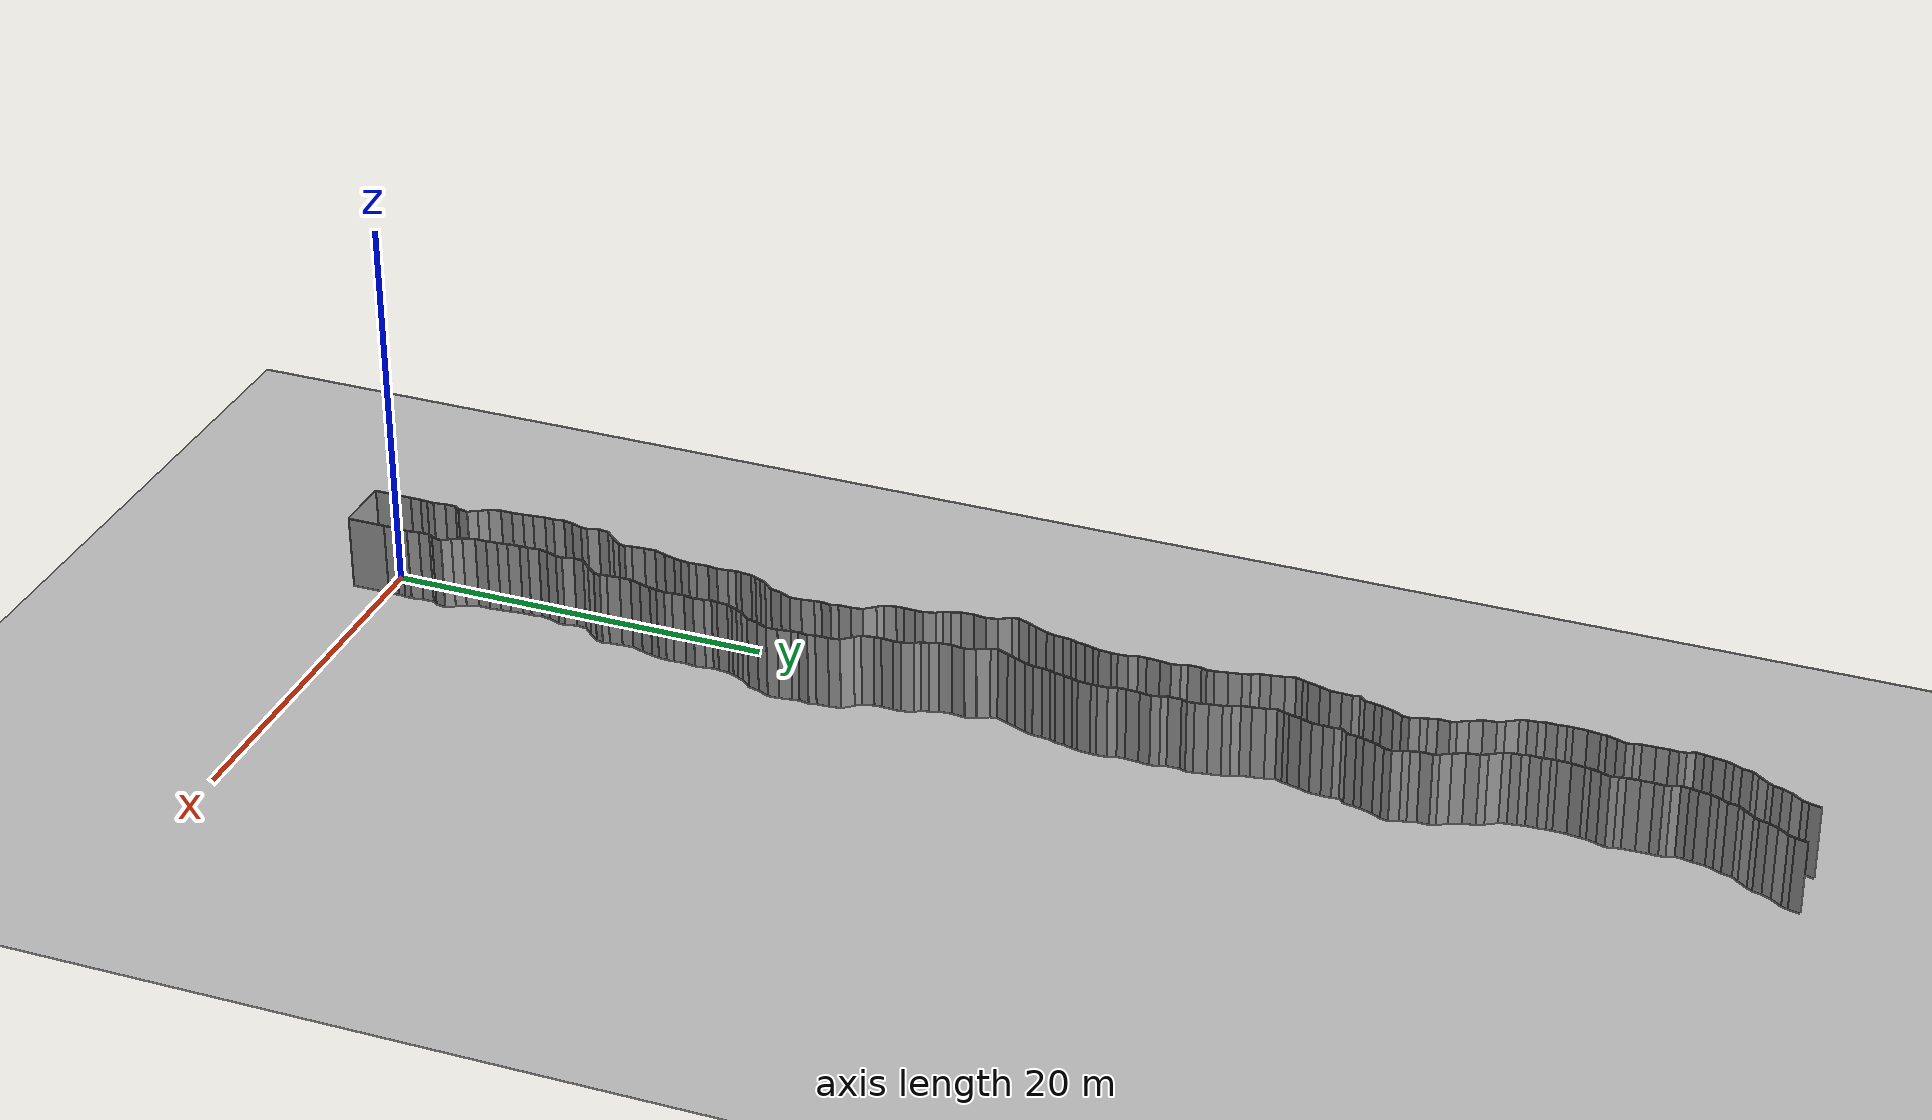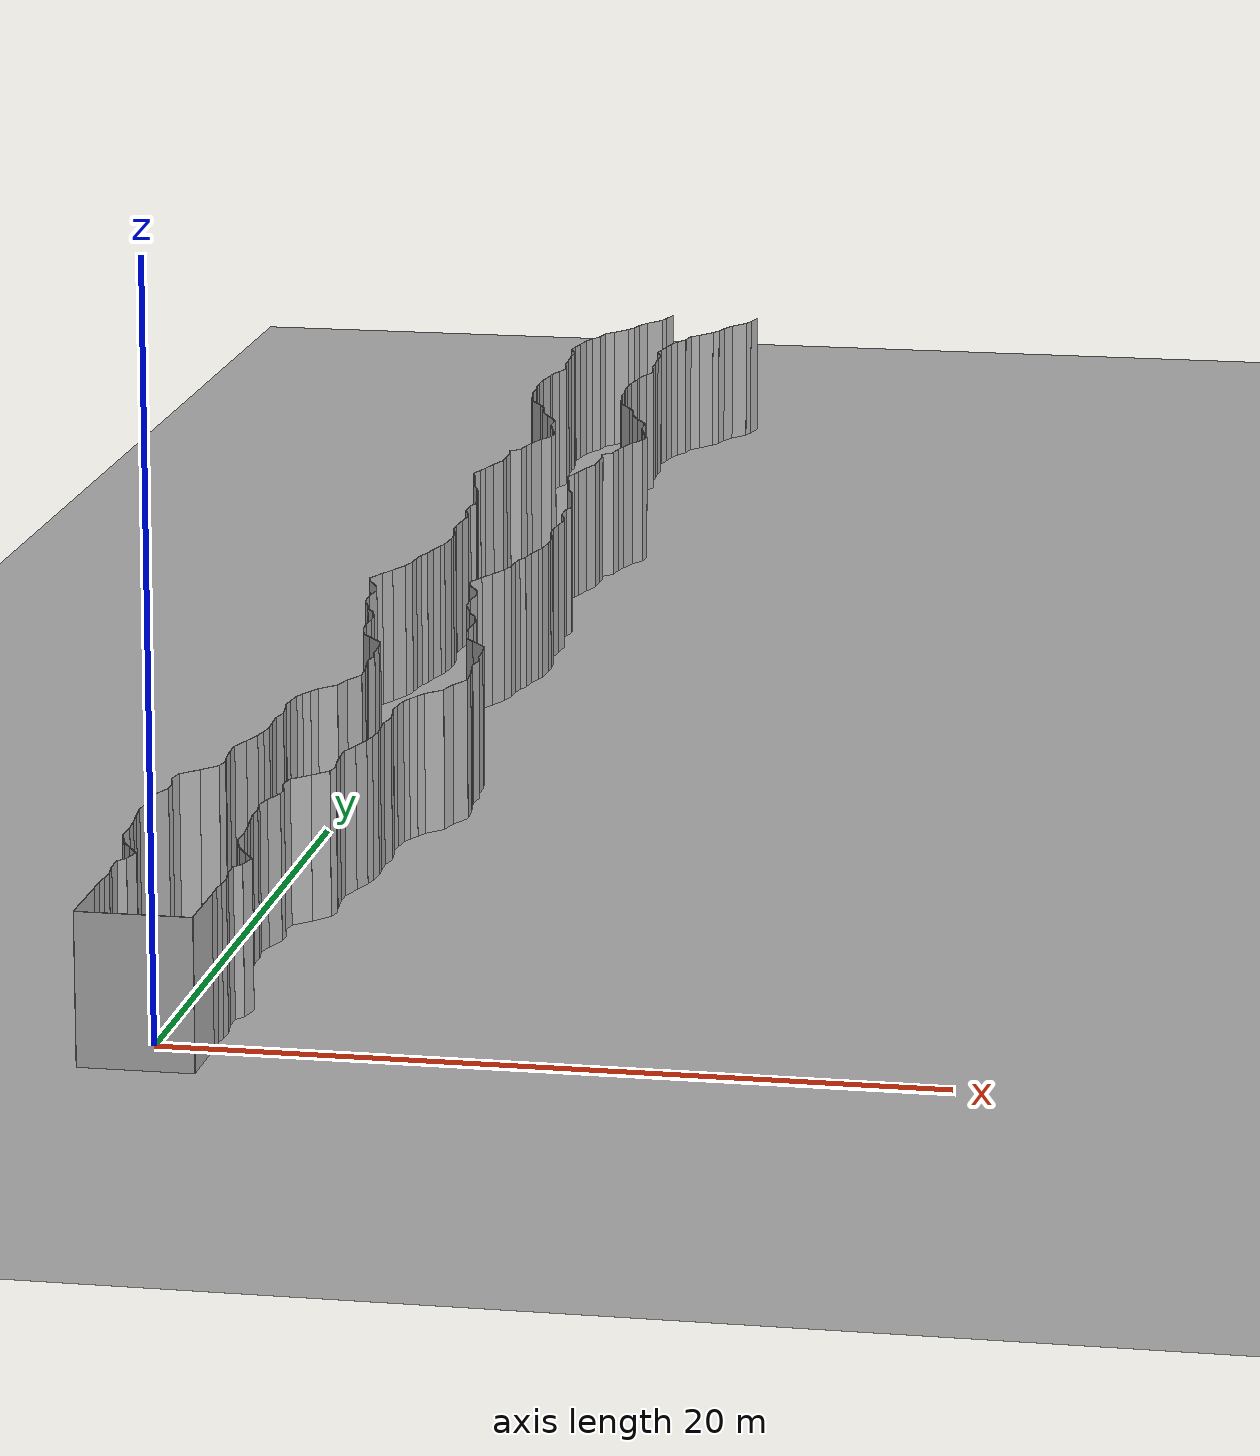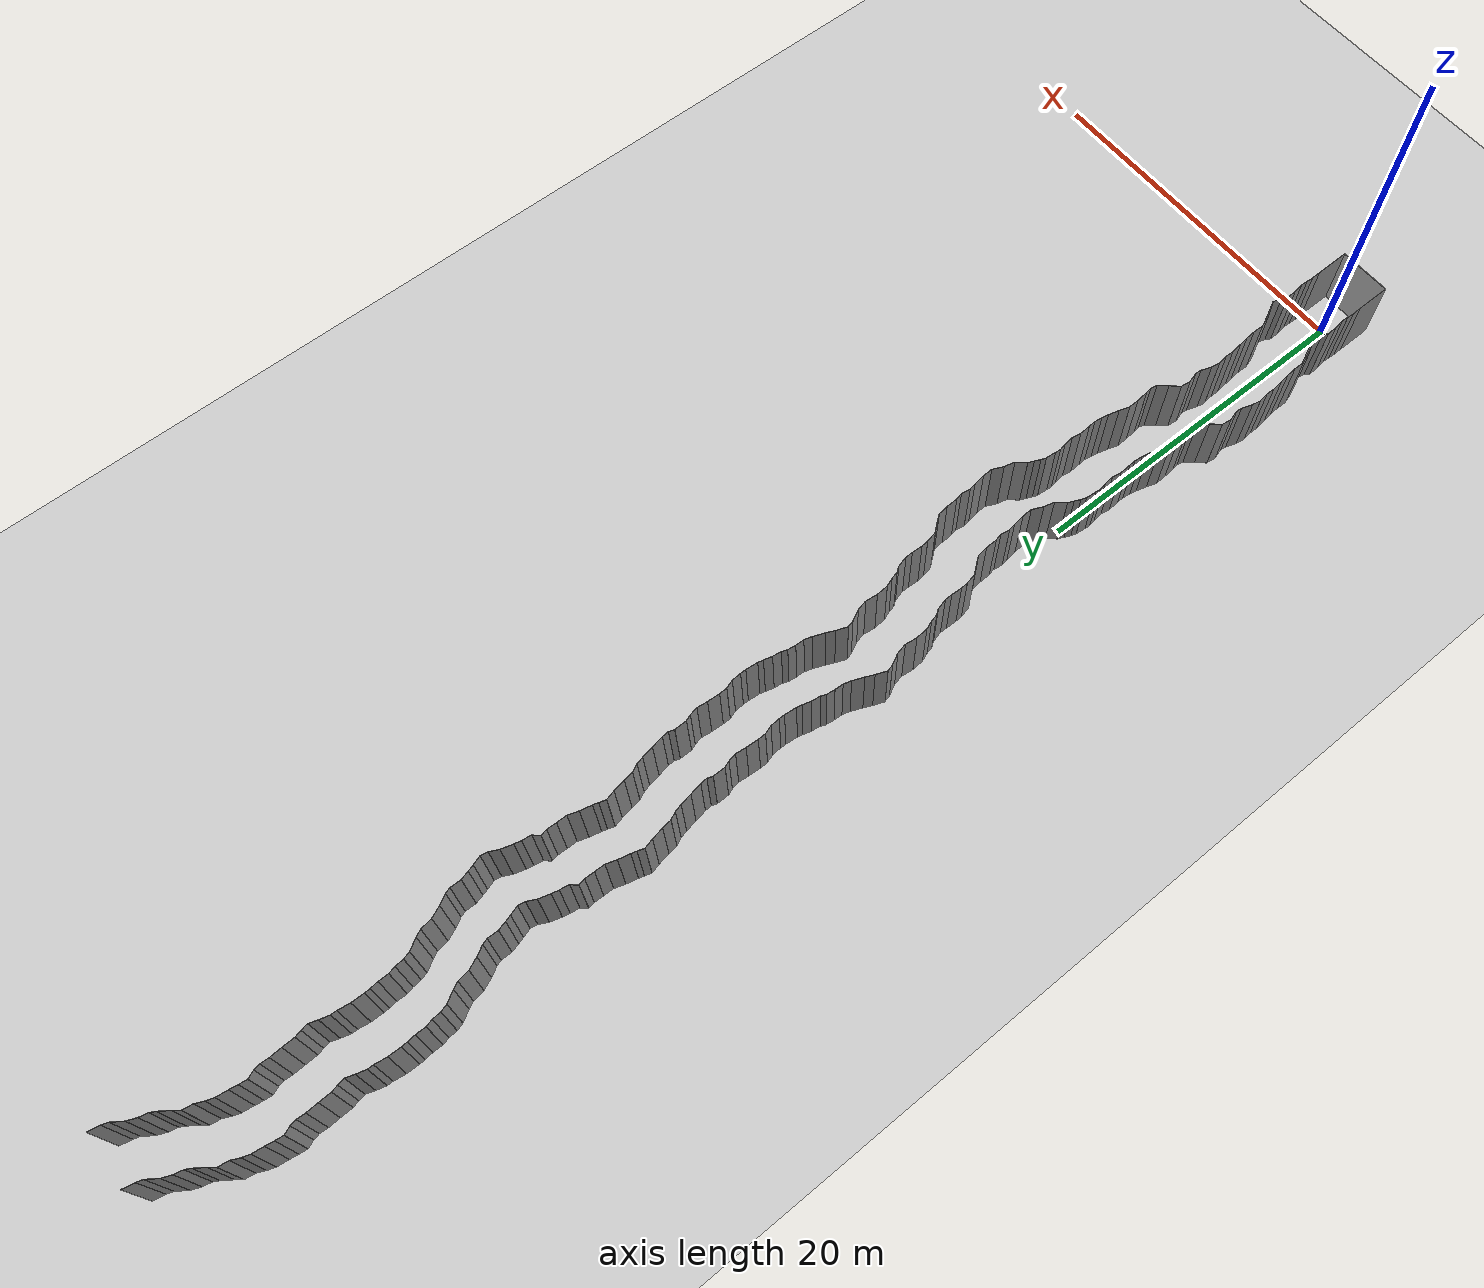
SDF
<sdf version="1.6">
 <world name="default">
  <light name="sun" type="directional">
   <pose>0 0 10 0 -0 0</pose>
   <diffuse>0.8 0.8 0.8 1</diffuse>
   <specular>0.2 0.2 0.2 1</specular>
   <attenuation>
    <range>1000</range>
    <constant>0.9</constant>
    <linear>0.01</linear>
    <quadratic>0.001</quadratic>
   </attenuation>
   <direction>-0.5 0.1 -0.9</direction>
  </light>
  <model name="ground_plane">
   <static>1</static>
   <link name="link">
    <collision name="collision">
     <geometry><plane><normal>0 0 1</normal><size>200 200</size></plane></geometry>
     <surface><friction><ode><mu>100</mu><mu2>50</mu2></ode></friction></surface>
    </collision>
    <visual name="visual">
     <cast_shadows>0</cast_shadows>
     <geometry><plane><normal>0 0 1</normal><size>200 200</size></plane></geometry>
     <material>
      <script><uri>file://media/materials/scripts/gazebo.material</uri><name>Gazebo/Grey</name></script>
     </material>
    </visual>
   </link>
   <pose>0 100 0 0 -0 0</pose>
  </model>
  <gravity>0 0 -9.8</gravity>
  <magnetic_field>6e-06 2.3e-05 -4.2e-05</magnetic_field>
  <atmosphere type="adiabatic"/>
  <physics default="0" name="default_physics" type="ode">
   <max_step_size>0.001</max_step_size>
   <real_time_factor>1</real_time_factor>
   <real_time_update_rate>1000</real_time_update_rate>
  </physics>
  <scene><ambient>0.4 0.4 0.4 1</ambient><background>0.7 0.7 0.7 1</background><shadows>1</shadows></scene>
  <spherical_coordinates>
   <surface_model>EARTH_WGS84</surface_model>
   <latitude_deg>0</latitude_deg>
   <longitude_deg>0</longitude_deg>
   <elevation>0</elevation>
   <heading_deg>0</heading_deg>
  </spherical_coordinates>
  <model name="wall_back">
   <static>1</static>
   <pose>0.0 -2 2 0.0 0 0.0</pose>
   <link name="link">
    <collision name="collision"><geometry><box><size>3 0.02 4</size></box></geometry></collision>
    <visual name="visual">
     <material>
      <script><name>Gazebo/Grey</name><uri>file://media/materials/scripts/gazebo.material</uri></script>
     </material>
     <geometry><box><size>3 0.02 4</size></box></geometry>
    </visual>
   </link>
  </model>
  <model name="wall_left">
   <static>1</static>
   <pose>1.5 -1 2 0 0 0.00</pose>
   <link name="link">
    <collision name="collision"><geometry><box><size>0.02 2 4</size></box></geometry></collision>
    <visual name="visual">
     <material>
      <script><name>Gazebo/Grey</name><uri>file://media/materials/scripts/gazebo.material</uri></script>
     </material>
     <geometry><box><size>0.02 2 4</size></box></geometry>
    </visual>
   </link>
  </model>
  <model name="wall_right">
   <static>1</static>
   <pose>-1.5 -1 2 0 0 0.00</pose>
   <link name="link">
    <collision name="collision"><geometry><box><size>0.02 2 4</size></box></geometry></collision>
    <visual name="visual">
     <material>
      <script><name>Gazebo/Grey</name><uri>file://media/materials/scripts/gazebo.material</uri></script>
     </material>
     <geometry><box><size>0.02 2 4</size></box></geometry>
    </visual>
   </link>
  </model>
  <model name="wall_0">
   <static>1</static>
   <pose>-1.5054074927113055 0.2771026538506849 2 0 0 0.01951192592504633</pose>
   <link name="link">
    <collision name="collision"><geometry><box><size>0.02 0.554310821646 4</size></box></geometry></collision>
    <visual name="visual">
     <material>
      <script><name>Gazebo/Grey</name><uri>file://media/materials/scripts/gazebo.material</uri></script>
     </material>
     <geometry><box><size>0.02 0.554310821646 4</size></box></geometry>
    </visual>
   </link>
  </model>
  <model name="wall_1">
   <static>1</static>
   <pose>1.4945925072886945 0.2771026538506849 2 0 0 0.01951192592504633</pose>
   <link name="link">
    <collision name="collision"><geometry><box><size>0.02 0.554310821646 4</size></box></geometry></collision>
    <visual name="visual">
     <material>
      <script><name>Gazebo/Grey</name><uri>file://media/materials/scripts/gazebo.material</uri></script>
     </material>
     <geometry><box><size>0.02 0.554310821646 4</size></box></geometry>
    </visual>
   </link>
  </model>
  <model name="wall_2">
   <static>1</static>
   <pose>-1.4959044309255267 0.7502712776522686 2 0 0 -0.0759025611334684</pose>
   <link name="link">
    <collision name="collision"><geometry><box><size>0.02 0.393264232842 4</size></box></geometry></collision>
    <visual name="visual">
     <material>
      <script><name>Gazebo/Grey</name><uri>file://media/materials/scripts/gazebo.material</uri></script>
     </material>
     <geometry><box><size>0.02 0.393264232842 4</size></box></geometry>
    </visual>
   </link>
  </model>
  <model name="wall_3">
   <static>1</static>
   <pose>1.5040955690744733 0.7502712776522686 2 0 0 -0.0759025611334684</pose>
   <link name="link">
    <collision name="collision"><geometry><box><size>0.02 0.393264232842 4</size></box></geometry></collision>
    <visual name="visual">
     <material>
      <script><name>Gazebo/Grey</name><uri>file://media/materials/scripts/gazebo.material</uri></script>
     </material>
     <geometry><box><size>0.02 0.393264232842 4</size></box></geometry>
    </visual>
   </link>
  </model>
  <model name="wall_4">
   <static>1</static>
   <pose>-1.4643491921734009 1.134139191659948 2 0 0 -0.0883979491608856</pose>
   <link name="link">
    <collision name="collision"><geometry><box><size>0.02 0.377076202938 4</size></box></geometry></collision>
    <visual name="visual">
     <material>
      <script><name>Gazebo/Grey</name><uri>file://media/materials/scripts/gazebo.material</uri></script>
     </material>
     <geometry><box><size>0.02 0.377076202938 4</size></box></geometry>
    </visual>
   </link>
  </model>
  <model name="wall_5">
   <static>1</static>
   <pose>1.5356508078265991 1.134139191659948 2 0 0 -0.0883979491608856</pose>
   <link name="link">
    <collision name="collision"><geometry><box><size>0.02 0.377076202938 4</size></box></geometry></collision>
    <visual name="visual">
     <material>
      <script><name>Gazebo/Grey</name><uri>file://media/materials/scripts/gazebo.material</uri></script>
     </material>
     <geometry><box><size>0.02 0.377076202938 4</size></box></geometry>
    </visual>
   </link>
  </model>
  <model name="wall_6">
   <static>1</static>
   <pose>-1.4956004174545228 1.6342153116711633 2 0 0 0.15219171952678584</pose>
   <link name="link">
    <collision name="collision"><geometry><box><size>0.02 0.631851815281 4</size></box></geometry></collision>
    <visual name="visual">
     <material>
      <script><name>Gazebo/Grey</name><uri>file://media/materials/scripts/gazebo.material</uri></script>
     </material>
     <geometry><box><size>0.02 0.631851815281 4</size></box></geometry>
    </visual>
   </link>
  </model>
  <model name="wall_7">
   <static>1</static>
   <pose>1.5043995825454772 1.6342153116711633 2 0 0 0.15219171952678584</pose>
   <link name="link">
    <collision name="collision"><geometry><box><size>0.02 0.631851815281 4</size></box></geometry></collision>
    <visual name="visual">
     <material>
      <script><name>Gazebo/Grey</name><uri>file://media/materials/scripts/gazebo.material</uri></script>
     </material>
     <geometry><box><size>0.02 0.631851815281 4</size></box></geometry>
    </visual>
   </link>
  </model>
  <model name="wall_8">
   <static>1</static>
   <pose>-1.5485579459105738 2.2367578282285723 2 0 0 0.017435955871296434</pose>
   <link name="link">
    <collision name="collision"><geometry><box><size>0.02 0.580624937606 4</size></box></geometry></collision>
    <visual name="visual">
     <material>
      <script><name>Gazebo/Grey</name><uri>file://media/materials/scripts/gazebo.material</uri></script>
     </material>
     <geometry><box><size>0.02 0.580624937606 4</size></box></geometry>
    </visual>
   </link>
  </model>
  <model name="wall_9">
   <static>1</static>
   <pose>1.4514420540894262 2.2367578282285723 2 0 0 0.017435955871296434</pose>
   <link name="link">
    <collision name="collision"><geometry><box><size>0.02 0.580624937606 4</size></box></geometry></collision>
    <visual name="visual">
     <material>
      <script><name>Gazebo/Grey</name><uri>file://media/materials/scripts/gazebo.material</uri></script>
     </material>
     <geometry><box><size>0.02 0.580624937606 4</size></box></geometry>
    </visual>
   </link>
  </model>
  <model name="wall_10">
   <static>1</static>
   <pose>-1.462039240900548 2.654437864276564 2 0 0 -0.6232157235891173</pose>
   <link name="link">
    <collision name="collision"><geometry><box><size>0.02 0.313819667117 4</size></box></geometry></collision>
    <visual name="visual">
     <material>
      <script><name>Gazebo/Grey</name><uri>file://media/materials/scripts/gazebo.material</uri></script>
     </material>
     <geometry><box><size>0.02 0.313819667117 4</size></box></geometry>
    </visual>
   </link>
  </model>
  <model name="wall_11">
   <static>1</static>
   <pose>1.537960759099452 2.654437864276564 2 0 0 -0.6232157235891173</pose>
   <link name="link">
    <collision name="collision"><geometry><box><size>0.02 0.313819667117 4</size></box></geometry></collision>
    <visual name="visual">
     <material>
      <script><name>Gazebo/Grey</name><uri>file://media/materials/scripts/gazebo.material</uri></script>
     </material>
     <geometry><box><size>0.02 0.313819667117 4</size></box></geometry>
    </visual>
   </link>
  </model>
  <model name="wall_12">
   <static>1</static>
   <pose>-1.3113700297301076 3.058214808628439 2 0 0 -0.21063580695061418</pose>
   <link name="link">
    <collision name="collision"><geometry><box><size>0.02 0.565222955651 4</size></box></geometry></collision>
    <visual name="visual">
     <material>
      <script><name>Gazebo/Grey</name><uri>file://media/materials/scripts/gazebo.material</uri></script>
     </material>
     <geometry><box><size>0.02 0.565222955651 4</size></box></geometry>
    </visual>
   </link>
  </model>
  <model name="wall_13">
   <static>1</static>
   <pose>1.6886299702698924 3.058214808628439 2 0 0 -0.21063580695061418</pose>
   <link name="link">
    <collision name="collision"><geometry><box><size>0.02 0.565222955651 4</size></box></geometry></collision>
    <visual name="visual">
     <material>
      <script><name>Gazebo/Grey</name><uri>file://media/materials/scripts/gazebo.material</uri></script>
     </material>
     <geometry><box><size>0.02 0.565222955651 4</size></box></geometry>
    </visual>
   </link>
  </model>
  <model name="wall_14">
   <static>1</static>
   <pose>-1.387883242274648 3.5617061277047846 2 0 0 0.5382361326546208</pose>
   <link name="link">
    <collision name="collision"><geometry><box><size>0.02 0.529052667385 4</size></box></geometry></collision>
    <visual name="visual">
     <material>
      <script><name>Gazebo/Grey</name><uri>file://media/materials/scripts/gazebo.material</uri></script>
     </material>
     <geometry><box><size>0.02 0.529052667385 4</size></box></geometry>
    </visual>
   </link>
  </model>
  <model name="wall_15">
   <static>1</static>
   <pose>1.612116757725352 3.5617061277047846 2 0 0 0.5382361326546208</pose>
   <link name="link">
    <collision name="collision"><geometry><box><size>0.02 0.529052667385 4</size></box></geometry></collision>
    <visual name="visual">
     <material>
      <script><name>Gazebo/Grey</name><uri>file://media/materials/scripts/gazebo.material</uri></script>
     </material>
     <geometry><box><size>0.02 0.529052667385 4</size></box></geometry>
    </visual>
   </link>
  </model>
  <model name="wall_16">
   <static>1</static>
   <pose>-1.6585811992603445 4.029327164597183 2 0 0 0.5118126217211321</pose>
   <link name="link">
    <collision name="collision"><geometry><box><size>0.02 0.55168367622 4</size></box></geometry></collision>
    <visual name="visual">
     <material>
      <script><name>Gazebo/Grey</name><uri>file://media/materials/scripts/gazebo.material</uri></script>
     </material>
     <geometry><box><size>0.02 0.55168367622 4</size></box></geometry>
    </visual>
   </link>
  </model>
  <model name="wall_17">
   <static>1</static>
   <pose>1.3414188007396555 4.029327164597183 2 0 0 0.5118126217211321</pose>
   <link name="link">
    <collision name="collision"><geometry><box><size>0.02 0.55168367622 4</size></box></geometry></collision>
    <visual name="visual">
     <material>
      <script><name>Gazebo/Grey</name><uri>file://media/materials/scripts/gazebo.material</uri></script>
     </material>
     <geometry><box><size>0.02 0.55168367622 4</size></box></geometry>
    </visual>
   </link>
  </model>
  <model name="wall_18">
   <static>1</static>
   <pose>-1.8909177781409472 4.583250966037759 2 0 0 0.3008320638870248</pose>
   <link name="link">
    <collision name="collision"><geometry><box><size>0.02 0.656333428633 4</size></box></geometry></collision>
    <visual name="visual">
     <material>
      <script><name>Gazebo/Grey</name><uri>file://media/materials/scripts/gazebo.material</uri></script>
     </material>
     <geometry><box><size>0.02 0.656333428633 4</size></box></geometry>
    </visual>
   </link>
  </model>
  <model name="wall_19">
   <static>1</static>
   <pose>1.1090822218590528 4.583250966037759 2 0 0 0.3008320638870248</pose>
   <link name="link">
    <collision name="collision"><geometry><box><size>0.02 0.656333428633 4</size></box></geometry></collision>
    <visual name="visual">
     <material>
      <script><name>Gazebo/Grey</name><uri>file://media/materials/scripts/gazebo.material</uri></script>
     </material>
     <geometry><box><size>0.02 0.656333428633 4</size></box></geometry>
    </visual>
   </link>
  </model>
  <model name="wall_20">
   <static>1</static>
   <pose>-1.9805885233839635 5.206537923220193 2 0 0 -0.02442560122571733</pose>
   <link name="link">
    <collision name="collision"><geometry><box><size>0.02 0.619901155349 4</size></box></geometry></collision>
    <visual name="visual">
     <material>
      <script><name>Gazebo/Grey</name><uri>file://media/materials/scripts/gazebo.material</uri></script>
     </material>
     <geometry><box><size>0.02 0.619901155349 4</size></box></geometry>
    </visual>
   </link>
  </model>
  <model name="wall_21">
   <static>1</static>
   <pose>1.0194114766160365 5.206537923220193 2 0 0 -0.02442560122571733</pose>
   <link name="link">
    <collision name="collision"><geometry><box><size>0.02 0.619901155349 4</size></box></geometry></collision>
    <visual name="visual">
     <material>
      <script><name>Gazebo/Grey</name><uri>file://media/materials/scripts/gazebo.material</uri></script>
     </material>
     <geometry><box><size>0.02 0.619901155349 4</size></box></geometry>
    </visual>
   </link>
  </model>
  <model name="wall_22">
   <static>1</static>
   <pose>-1.9973362197201507 5.817134929957269 2 0 0 0.08068421558176188</pose>
   <link name="link">
    <collision name="collision"><geometry><box><size>0.02 0.603440885994 4</size></box></geometry></collision>
    <visual name="visual">
     <material>
      <script><name>Gazebo/Grey</name><uri>file://media/materials/scripts/gazebo.material</uri></script>
     </material>
     <geometry><box><size>0.02 0.603440885994 4</size></box></geometry>
    </visual>
   </link>
  </model>
  <model name="wall_23">
   <static>1</static>
   <pose>1.0026637802798493 5.817134929957269 2 0 0 0.08068421558176188</pose>
   <link name="link">
    <collision name="collision"><geometry><box><size>0.02 0.603440885994 4</size></box></geometry></collision>
    <visual name="visual">
     <material>
      <script><name>Gazebo/Grey</name><uri>file://media/materials/scripts/gazebo.material</uri></script>
     </material>
     <geometry><box><size>0.02 0.603440885994 4</size></box></geometry>
    </visual>
   </link>
  </model>
  <model name="wall_24">
   <static>1</static>
   <pose>-2.0521156811494174 6.386560087364572 2 0 0 0.11289104059538006</pose>
   <link name="link">
    <collision name="collision"><geometry><box><size>0.02 0.540815066134 4</size></box></geometry></collision>
    <visual name="visual">
     <material>
      <script><name>Gazebo/Grey</name><uri>file://media/materials/scripts/gazebo.material</uri></script>
     </material>
     <geometry><box><size>0.02 0.540815066134 4</size></box></geometry>
    </visual>
   </link>
  </model>
  <model name="wall_25">
   <static>1</static>
   <pose>0.9478843188505826 6.386560087364572 2 0 0 0.11289104059538006</pose>
   <link name="link">
    <collision name="collision"><geometry><box><size>0.02 0.540815066134 4</size></box></geometry></collision>
    <visual name="visual">
     <material>
      <script><name>Gazebo/Grey</name><uri>file://media/materials/scripts/gazebo.material</uri></script>
     </material>
     <geometry><box><size>0.02 0.540815066134 4</size></box></geometry>
    </visual>
   </link>
  </model>
  <model name="wall_26">
   <static>1</static>
   <pose>-2.118105277894146 6.975692398489997 2 0 0 0.11041890806038186</pose>
   <link name="link">
    <collision name="collision"><geometry><box><size>0.02 0.64481900844 4</size></box></geometry></collision>
    <visual name="visual">
     <material>
      <script><name>Gazebo/Grey</name><uri>file://media/materials/scripts/gazebo.material</uri></script>
     </material>
     <geometry><box><size>0.02 0.64481900844 4</size></box></geometry>
    </visual>
   </link>
  </model>
  <model name="wall_27">
   <static>1</static>
   <pose>0.8818947221058542 6.975692398489997 2 0 0 0.11041890806038186</pose>
   <link name="link">
    <collision name="collision"><geometry><box><size>0.02 0.64481900844 4</size></box></geometry></collision>
    <visual name="visual">
     <material>
      <script><name>Gazebo/Grey</name><uri>file://media/materials/scripts/gazebo.material</uri></script>
     </material>
     <geometry><box><size>0.02 0.64481900844 4</size></box></geometry>
    </visual>
   </link>
  </model>
  <model name="wall_28">
   <static>1</static>
   <pose>-2.144456496622843 7.5351797083397845 2 0 0 -0.038370300423932795</pose>
   <link name="link">
    <collision name="collision"><geometry><box><size>0.02 0.478434695416 4</size></box></geometry></collision>
    <visual name="visual">
     <material>
      <script><name>Gazebo/Grey</name><uri>file://media/materials/scripts/gazebo.material</uri></script>
     </material>
     <geometry><box><size>0.02 0.478434695416 4</size></box></geometry>
    </visual>
   </link>
  </model>
  <model name="wall_29">
   <static>1</static>
   <pose>0.8555435033771568 7.5351797083397845 2 0 0 -0.038370300423932795</pose>
   <link name="link">
    <collision name="collision"><geometry><box><size>0.02 0.478434695416 4</size></box></geometry></collision>
    <visual name="visual">
     <material>
      <script><name>Gazebo/Grey</name><uri>file://media/materials/scripts/gazebo.material</uri></script>
     </material>
     <geometry><box><size>0.02 0.478434695416 4</size></box></geometry>
    </visual>
   </link>
  </model>
  <model name="wall_30">
   <static>1</static>
   <pose>-2.1742142331606984 8.060168310753168 2 0 0 0.135326887934024</pose>
   <link name="link">
    <collision name="collision"><geometry><box><size>0.02 0.577171577901 4</size></box></geometry></collision>
    <visual name="visual">
     <material>
      <script><name>Gazebo/Grey</name><uri>file://media/materials/scripts/gazebo.material</uri></script>
     </material>
     <geometry><box><size>0.02 0.577171577901 4</size></box></geometry>
    </visual>
   </link>
  </model>
  <model name="wall_31">
   <static>1</static>
   <pose>0.8257857668393016 8.060168310753168 2 0 0 0.135326887934024</pose>
   <link name="link">
    <collision name="collision"><geometry><box><size>0.02 0.577171577901 4</size></box></geometry></collision>
    <visual name="visual">
     <material>
      <script><name>Gazebo/Grey</name><uri>file://media/materials/scripts/gazebo.material</uri></script>
     </material>
     <geometry><box><size>0.02 0.577171577901 4</size></box></geometry>
    </visual>
   </link>
  </model>
  <model name="wall_32">
   <static>1</static>
   <pose>-2.1672094972830904 8.588856348511438 2 0 0 -0.18703950172446787</pose>
   <link name="link">
    <collision name="collision"><geometry><box><size>0.02 0.494098971182 4</size></box></geometry></collision>
    <visual name="visual">
     <material>
      <script><name>Gazebo/Grey</name><uri>file://media/materials/scripts/gazebo.material</uri></script>
     </material>
     <geometry><box><size>0.02 0.494098971182 4</size></box></geometry>
    </visual>
   </link>
  </model>
  <model name="wall_33">
   <static>1</static>
   <pose>0.8327905027169096 8.588856348511438 2 0 0 -0.18703950172446787</pose>
   <link name="link">
    <collision name="collision"><geometry><box><size>0.02 0.494098971182 4</size></box></geometry></collision>
    <visual name="visual">
     <material>
      <script><name>Gazebo/Grey</name><uri>file://media/materials/scripts/gazebo.material</uri></script>
     </material>
     <geometry><box><size>0.02 0.494098971182 4</size></box></geometry>
    </visual>
   </link>
  </model>
  <model name="wall_34">
   <static>1</static>
   <pose>-2.015668417744564 9.131479882684664 2 0 0 -0.33858379931227994</pose>
   <link name="link">
    <collision name="collision"><geometry><box><size>0.02 0.635866325784 4</size></box></geometry></collision>
    <visual name="visual">
     <material>
      <script><name>Gazebo/Grey</name><uri>file://media/materials/scripts/gazebo.material</uri></script>
     </material>
     <geometry><box><size>0.02 0.635866325784 4</size></box></geometry>
    </visual>
   </link>
  </model>
  <model name="wall_35">
   <static>1</static>
   <pose>0.9843315822554359 9.131479882684664 2 0 0 -0.33858379931227994</pose>
   <link name="link">
    <collision name="collision"><geometry><box><size>0.02 0.635866325784 4</size></box></geometry></collision>
    <visual name="visual">
     <material>
      <script><name>Gazebo/Grey</name><uri>file://media/materials/scripts/gazebo.material</uri></script>
     </material>
     <geometry><box><size>0.02 0.635866325784 4</size></box></geometry>
    </visual>
   </link>
  </model>
  <model name="wall_36">
   <static>1</static>
   <pose>-1.8993605516469905 9.607418675851601 2 0 0 -0.06073455969819481</pose>
   <link name="link">
    <collision name="collision"><geometry><box><size>0.02 0.352762347324 4</size></box></geometry></collision>
    <visual name="visual">
     <material>
      <script><name>Gazebo/Grey</name><uri>file://media/materials/scripts/gazebo.material</uri></script>
     </material>
     <geometry><box><size>0.02 0.352762347324 4</size></box></geometry>
    </visual>
   </link>
  </model>
  <model name="wall_37">
   <static>1</static>
   <pose>1.1006394483530095 9.607418675851601 2 0 0 -0.06073455969819481</pose>
   <link name="link">
    <collision name="collision"><geometry><box><size>0.02 0.352762347324 4</size></box></geometry></collision>
    <visual name="visual">
     <material>
      <script><name>Gazebo/Grey</name><uri>file://media/materials/scripts/gazebo.material</uri></script>
     </material>
     <geometry><box><size>0.02 0.352762347324 4</size></box></geometry>
    </visual>
   </link>
  </model>
  <model name="wall_38">
   <static>1</static>
   <pose>-1.9698788280360264 10.072827773237233 2 0 0 0.2736663470046549</pose>
   <link name="link">
    <collision name="collision"><geometry><box><size>0.02 0.601074348031 4</size></box></geometry></collision>
    <visual name="visual">
     <material>
      <script><name>Gazebo/Grey</name><uri>file://media/materials/scripts/gazebo.material</uri></script>
     </material>
     <geometry><box><size>0.02 0.601074348031 4</size></box></geometry>
    </visual>
   </link>
  </model>
  <model name="wall_39">
   <static>1</static>
   <pose>1.0301211719639736 10.072827773237233 2 0 0 0.2736663470046549</pose>
   <link name="link">
    <collision name="collision"><geometry><box><size>0.02 0.601074348031 4</size></box></geometry></collision>
    <visual name="visual">
     <material>
      <script><name>Gazebo/Grey</name><uri>file://media/materials/scripts/gazebo.material</uri></script>
     </material>
     <geometry><box><size>0.02 0.601074348031 4</size></box></geometry>
    </visual>
   </link>
  </model>
  <model name="wall_40">
   <static>1</static>
   <pose>-2.0156612284845594 10.640264472965416 2 0 0 -0.1267664764820144</pose>
   <link name="link">
    <collision name="collision"><geometry><box><size>0.02 0.560665985813 4</size></box></geometry></collision>
    <visual name="visual">
     <material>
      <script><name>Gazebo/Grey</name><uri>file://media/materials/scripts/gazebo.material</uri></script>
     </material>
     <geometry><box><size>0.02 0.560665985813 4</size></box></geometry>
    </visual>
   </link>
  </model>
  <model name="wall_41">
   <static>1</static>
   <pose>0.9843387715154406 10.640264472965416 2 0 0 -0.1267664764820144</pose>
   <link name="link">
    <collision name="collision"><geometry><box><size>0.02 0.560665985813 4</size></box></geometry></collision>
    <visual name="visual">
     <material>
      <script><name>Gazebo/Grey</name><uri>file://media/materials/scripts/gazebo.material</uri></script>
     </material>
     <geometry><box><size>0.02 0.560665985813 4</size></box></geometry>
    </visual>
   </link>
  </model>
  <model name="wall_42">
   <static>1</static>
   <pose>-1.756125133555819 11.155642570887409 2 0 0 -0.7567963504653398</pose>
   <link name="link">
    <collision name="collision"><geometry><box><size>0.02 0.652769425243 4</size></box></geometry></collision>
    <visual name="visual">
     <material>
      <script><name>Gazebo/Grey</name><uri>file://media/materials/scripts/gazebo.material</uri></script>
     </material>
     <geometry><box><size>0.02 0.652769425243 4</size></box></geometry>
    </visual>
   </link>
  </model>
  <model name="wall_43">
   <static>1</static>
   <pose>1.243874866444181 11.155642570887409 2 0 0 -0.7567963504653398</pose>
   <link name="link">
    <collision name="collision"><geometry><box><size>0.02 0.652769425243 4</size></box></geometry></collision>
    <visual name="visual">
     <material>
      <script><name>Gazebo/Grey</name><uri>file://media/materials/scripts/gazebo.material</uri></script>
     </material>
     <geometry><box><size>0.02 0.652769425243 4</size></box></geometry>
    </visual>
   </link>
  </model>
  <model name="wall_44">
   <static>1</static>
   <pose>-1.3314973967981687 11.641816773508703 2 0 0 -0.6782337334837881</pose>
   <link name="link">
    <collision name="collision"><geometry><box><size>0.02 0.63923304881 4</size></box></geometry></collision>
    <visual name="visual">
     <material>
      <script><name>Gazebo/Grey</name><uri>file://media/materials/scripts/gazebo.material</uri></script>
     </material>
     <geometry><box><size>0.02 0.63923304881 4</size></box></geometry>
    </visual>
   </link>
  </model>
  <model name="wall_45">
   <static>1</static>
   <pose>1.6685026032018313 11.641816773508703 2 0 0 -0.6782337334837881</pose>
   <link name="link">
    <collision name="collision"><geometry><box><size>0.02 0.63923304881 4</size></box></geometry></collision>
    <visual name="visual">
     <material>
      <script><name>Gazebo/Grey</name><uri>file://media/materials/scripts/gazebo.material</uri></script>
     </material>
     <geometry><box><size>0.02 0.63923304881 4</size></box></geometry>
    </visual>
   </link>
  </model>
  <model name="wall_46">
   <static>1</static>
   <pose>-1.0887344343260754 12.073601627640796 2 0 0 -0.22690634049711625</pose>
   <link name="link">
    <collision name="collision"><geometry><box><size>0.02 0.375433850401 4</size></box></geometry></collision>
    <visual name="visual">
     <material>
      <script><name>Gazebo/Grey</name><uri>file://media/materials/scripts/gazebo.material</uri></script>
     </material>
     <geometry><box><size>0.02 0.375433850401 4</size></box></geometry>
    </visual>
   </link>
  </model>
  <model name="wall_47">
   <static>1</static>
   <pose>1.9112655656739246 12.073601627640796 2 0 0 -0.22690634049711625</pose>
   <link name="link">
    <collision name="collision"><geometry><box><size>0.02 0.375433850401 4</size></box></geometry></collision>
    <visual name="visual">
     <material>
      <script><name>Gazebo/Grey</name><uri>file://media/materials/scripts/gazebo.material</uri></script>
     </material>
     <geometry><box><size>0.02 0.375433850401 4</size></box></geometry>
    </visual>
   </link>
  </model>
  <model name="wall_48">
   <static>1</static>
   <pose>-1.0788543452916426 12.437245227300805 2 0 0 0.17710984068795022</pose>
   <link name="link">
    <collision name="collision"><geometry><box><size>0.02 0.367221277398 4</size></box></geometry></collision>
    <visual name="visual">
     <material>
      <script><name>Gazebo/Grey</name><uri>file://media/materials/scripts/gazebo.material</uri></script>
     </material>
     <geometry><box><size>0.02 0.367221277398 4</size></box></geometry>
    </visual>
   </link>
  </model>
  <model name="wall_49">
   <static>1</static>
   <pose>1.9211456547083574 12.437245227300805 2 0 0 0.17710984068795022</pose>
   <link name="link">
    <collision name="collision"><geometry><box><size>0.02 0.367221277398 4</size></box></geometry></collision>
    <visual name="visual">
     <material>
      <script><name>Gazebo/Grey</name><uri>file://media/materials/scripts/gazebo.material</uri></script>
     </material>
     <geometry><box><size>0.02 0.367221277398 4</size></box></geometry>
    </visual>
   </link>
  </model>
  <model name="wall_50">
   <static>1</static>
   <pose>-1.1404934638177369 12.956281659625823 2 0 0 0.08636395326375335</pose>
   <link name="link">
    <collision name="collision"><geometry><box><size>0.02 0.67912716718 4</size></box></geometry></collision>
    <visual name="visual">
     <material>
      <script><name>Gazebo/Grey</name><uri>file://media/materials/scripts/gazebo.material</uri></script>
     </material>
     <geometry><box><size>0.02 0.67912716718 4</size></box></geometry>
    </visual>
   </link>
  </model>
  <model name="wall_51">
   <static>1</static>
   <pose>1.8595065361822631 12.956281659625823 2 0 0 0.08636395326375335</pose>
   <link name="link">
    <collision name="collision"><geometry><box><size>0.02 0.67912716718 4</size></box></geometry></collision>
    <visual name="visual">
     <material>
      <script><name>Gazebo/Grey</name><uri>file://media/materials/scripts/gazebo.material</uri></script>
     </material>
     <geometry><box><size>0.02 0.67912716718 4</size></box></geometry>
    </visual>
   </link>
  </model>
  <model name="wall_52">
   <static>1</static>
   <pose>-1.174903417268751 13.59281125453791 2 0 0 0.017167327511310754</pose>
   <link name="link">
    <collision name="collision"><geometry><box><size>0.02 0.596551067461 4</size></box></geometry></collision>
    <visual name="visual">
     <material>
      <script><name>Gazebo/Grey</name><uri>file://media/materials/scripts/gazebo.material</uri></script>
     </material>
     <geometry><box><size>0.02 0.596551067461 4</size></box></geometry>
    </visual>
   </link>
  </model>
  <model name="wall_53">
   <static>1</static>
   <pose>1.825096582731249 13.59281125453791 2 0 0 0.017167327511310754</pose>
   <link name="link">
    <collision name="collision"><geometry><box><size>0.02 0.596551067461 4</size></box></geometry></collision>
    <visual name="visual">
     <material>
      <script><name>Gazebo/Grey</name><uri>file://media/materials/scripts/gazebo.material</uri></script>
     </material>
     <geometry><box><size>0.02 0.596551067461 4</size></box></geometry>
    </visual>
   </link>
  </model>
  <model name="wall_54">
   <static>1</static>
   <pose>-1.0877183155078667 14.187900098017359 2 0 0 -0.3014650150407536</pose>
   <link name="link">
    <collision name="collision"><geometry><box><size>0.02 0.62175406415 4</size></box></geometry></collision>
    <visual name="visual">
     <material>
      <script><name>Gazebo/Grey</name><uri>file://media/materials/scripts/gazebo.material</uri></script>
     </material>
     <geometry><box><size>0.02 0.62175406415 4</size></box></geometry>
    </visual>
   </link>
  </model>
  <model name="wall_55">
   <static>1</static>
   <pose>1.9122816844921333 14.187900098017359 2 0 0 -0.3014650150407536</pose>
   <link name="link">
    <collision name="collision"><geometry><box><size>0.02 0.62175406415 4</size></box></geometry></collision>
    <visual name="visual">
     <material>
      <script><name>Gazebo/Grey</name><uri>file://media/materials/scripts/gazebo.material</uri></script>
     </material>
     <geometry><box><size>0.02 0.62175406415 4</size></box></geometry>
    </visual>
   </link>
  </model>
  <model name="wall_56">
   <static>1</static>
   <pose>-0.9094705302789531 14.786644750265983 2 0 0 -0.27734635519245476</pose>
   <link name="link">
    <collision name="collision"><geometry><box><size>0.02 0.627764549265 4</size></box></geometry></collision>
    <visual name="visual">
     <material>
      <script><name>Gazebo/Grey</name><uri>file://media/materials/scripts/gazebo.material</uri></script>
     </material>
     <geometry><box><size>0.02 0.627764549265 4</size></box></geometry>
    </visual>
   </link>
  </model>
  <model name="wall_57">
   <static>1</static>
   <pose>2.090529469721047 14.786644750265983 2 0 0 -0.27734635519245476</pose>
   <link name="link">
    <collision name="collision"><geometry><box><size>0.02 0.627764549265 4</size></box></geometry></collision>
    <visual name="visual">
     <material>
      <script><name>Gazebo/Grey</name><uri>file://media/materials/scripts/gazebo.material</uri></script>
     </material>
     <geometry><box><size>0.02 0.627764549265 4</size></box></geometry>
    </visual>
   </link>
  </model>
  <model name="wall_58">
   <static>1</static>
   <pose>-0.7868706307932595 15.287537107344864 2 0 0 -0.1821622284356912</pose>
   <link name="link">
    <collision name="collision"><geometry><box><size>0.02 0.404706083233 4</size></box></geometry></collision>
    <visual name="visual">
     <material>
      <script><name>Gazebo/Grey</name><uri>file://media/materials/scripts/gazebo.material</uri></script>
     </material>
     <geometry><box><size>0.02 0.404706083233 4</size></box></geometry>
    </visual>
   </link>
  </model>
  <model name="wall_59">
   <static>1</static>
   <pose>2.2131293692067406 15.287537107344864 2 0 0 -0.1821622284356912</pose>
   <link name="link">
    <collision name="collision"><geometry><box><size>0.02 0.404706083233 4</size></box></geometry></collision>
    <visual name="visual">
     <material>
      <script><name>Gazebo/Grey</name><uri>file://media/materials/scripts/gazebo.material</uri></script>
     </material>
     <geometry><box><size>0.02 0.404706083233 4</size></box></geometry>
    </visual>
   </link>
  </model>
  <model name="wall_60">
   <static>1</static>
   <pose>-0.7220999563080335 15.711231152706333 2 0 0 -0.12447322867208174</pose>
   <link name="link">
    <collision name="collision"><geometry><box><size>0.02 0.452882012264 4</size></box></geometry></collision>
    <visual name="visual">
     <material>
      <script><name>Gazebo/Grey</name><uri>file://media/materials/scripts/gazebo.material</uri></script>
     </material>
     <geometry><box><size>0.02 0.452882012264 4</size></box></geometry>
    </visual>
   </link>
  </model>
  <model name="wall_61">
   <static>1</static>
   <pose>2.2779000436919663 15.711231152706333 2 0 0 -0.12447322867208174</pose>
   <link name="link">
    <collision name="collision"><geometry><box><size>0.02 0.452882012264 4</size></box></geometry></collision>
    <visual name="visual">
     <material>
      <script><name>Gazebo/Grey</name><uri>file://media/materials/scripts/gazebo.material</uri></script>
     </material>
     <geometry><box><size>0.02 0.452882012264 4</size></box></geometry>
    </visual>
   </link>
  </model>
  <model name="wall_62">
   <static>1</static>
   <pose>-0.7067511571078383 16.140338599885162 2 0 0 0.062361158391564</pose>
   <link name="link">
    <collision name="collision"><geometry><box><size>0.02 0.409632993203 4</size></box></geometry></collision>
    <visual name="visual">
     <material>
      <script><name>Gazebo/Grey</name><uri>file://media/materials/scripts/gazebo.material</uri></script>
     </material>
     <geometry><box><size>0.02 0.409632993203 4</size></box></geometry>
    </visual>
   </link>
  </model>
  <model name="wall_63">
   <static>1</static>
   <pose>2.2932488428921616 16.140338599885162 2 0 0 0.062361158391564</pose>
   <link name="link">
    <collision name="collision"><geometry><box><size>0.02 0.409632993203 4</size></box></geometry></collision>
    <visual name="visual">
     <material>
      <script><name>Gazebo/Grey</name><uri>file://media/materials/scripts/gazebo.material</uri></script>
     </material>
     <geometry><box><size>0.02 0.409632993203 4</size></box></geometry>
    </visual>
   </link>
  </model>
  <model name="wall_64">
   <static>1</static>
   <pose>-0.7367128959855198 16.667386904536393 2 0 0 0.053253464668122086</pose>
   <link name="link">
    <collision name="collision"><geometry><box><size>0.02 0.646175910551 4</size></box></geometry></collision>
    <visual name="visual">
     <material>
      <script><name>Gazebo/Grey</name><uri>file://media/materials/scripts/gazebo.material</uri></script>
     </material>
     <geometry><box><size>0.02 0.646175910551 4</size></box></geometry>
    </visual>
   </link>
  </model>
  <model name="wall_65">
   <static>1</static>
   <pose>2.26328710401448 16.667386904536393 2 0 0 0.053253464668122086</pose>
   <link name="link">
    <collision name="collision"><geometry><box><size>0.02 0.646175910551 4</size></box></geometry></collision>
    <visual name="visual">
     <material>
      <script><name>Gazebo/Grey</name><uri>file://media/materials/scripts/gazebo.material</uri></script>
     </material>
     <geometry><box><size>0.02 0.646175910551 4</size></box></geometry>
    </visual>
   </link>
  </model>
  <model name="wall_66">
   <static>1</static>
   <pose>-0.7079828425071415 17.248373509878917 2 0 0 -0.1759298730560734</pose>
   <link name="link">
    <collision name="collision"><geometry><box><size>0.02 0.524814259136 4</size></box></geometry></collision>
    <visual name="visual">
     <material>
      <script><name>Gazebo/Grey</name><uri>file://media/materials/scripts/gazebo.material</uri></script>
     </material>
     <geometry><box><size>0.02 0.524814259136 4</size></box></geometry>
    </visual>
   </link>
  </model>
  <model name="wall_67">
   <static>1</static>
   <pose>2.2920171574928583 17.248373509878917 2 0 0 -0.1759298730560734</pose>
   <link name="link">
    <collision name="collision"><geometry><box><size>0.02 0.524814259136 4</size></box></geometry></collision>
    <visual name="visual">
     <material>
      <script><name>Gazebo/Grey</name><uri>file://media/materials/scripts/gazebo.material</uri></script>
     </material>
     <geometry><box><size>0.02 0.524814259136 4</size></box></geometry>
    </visual>
   </link>
  </model>
  <model name="wall_68">
   <static>1</static>
   <pose>-0.6925326112370563 17.78629782928836 2 0 0 0.10858682358184547</pose>
   <link name="link">
    <collision name="collision"><geometry><box><size>0.02 0.562447982671 4</size></box></geometry></collision>
    <visual name="visual">
     <material>
      <script><name>Gazebo/Grey</name><uri>file://media/materials/scripts/gazebo.material</uri></script>
     </material>
     <geometry><box><size>0.02 0.562447982671 4</size></box></geometry>
    </visual>
   </link>
  </model>
  <model name="wall_69">
   <static>1</static>
   <pose>2.3074673887629435 17.78629782928836 2 0 0 0.10858682358184547</pose>
   <link name="link">
    <collision name="collision"><geometry><box><size>0.02 0.562447982671 4</size></box></geometry></collision>
    <visual name="visual">
     <material>
      <script><name>Gazebo/Grey</name><uri>file://media/materials/scripts/gazebo.material</uri></script>
     </material>
     <geometry><box><size>0.02 0.562447982671 4</size></box></geometry>
    </visual>
   </link>
  </model>
  <model name="wall_70">
   <static>1</static>
   <pose>-0.7616740574755443 18.261685027293698 2 0 0 0.19494063190426525</pose>
   <link name="link">
    <collision name="collision"><geometry><box><size>0.02 0.399200280215 4</size></box></geometry></collision>
    <visual name="visual">
     <material>
      <script><name>Gazebo/Grey</name><uri>file://media/materials/scripts/gazebo.material</uri></script>
     </material>
     <geometry><box><size>0.02 0.399200280215 4</size></box></geometry>
    </visual>
   </link>
  </model>
  <model name="wall_71">
   <static>1</static>
   <pose>2.2383259425244555 18.261685027293698 2 0 0 0.19494063190426525</pose>
   <link name="link">
    <collision name="collision"><geometry><box><size>0.02 0.399200280215 4</size></box></geometry></collision>
    <visual name="visual">
     <material>
      <script><name>Gazebo/Grey</name><uri>file://media/materials/scripts/gazebo.material</uri></script>
     </material>
     <geometry><box><size>0.02 0.399200280215 4</size></box></geometry>
    </visual>
   </link>
  </model>
  <model name="wall_72">
   <static>1</static>
   <pose>-0.7809799024888369 18.608365236209874 2 0 0 -0.12762203050015697</pose>
   <link name="link">
    <collision name="collision"><geometry><box><size>0.02 0.304195233267 4</size></box></geometry></collision>
    <visual name="visual">
     <material>
      <script><name>Gazebo/Grey</name><uri>file://media/materials/scripts/gazebo.material</uri></script>
     </material>
     <geometry><box><size>0.02 0.304195233267 4</size></box></geometry>
    </visual>
   </link>
  </model>
  <model name="wall_73">
   <static>1</static>
   <pose>2.219020097511163 18.608365236209874 2 0 0 -0.12762203050015697</pose>
   <link name="link">
    <collision name="collision"><geometry><box><size>0.02 0.304195233267 4</size></box></geometry></collision>
    <visual name="visual">
     <material>
      <script><name>Gazebo/Grey</name><uri>file://media/materials/scripts/gazebo.material</uri></script>
     </material>
     <geometry><box><size>0.02 0.304195233267 4</size></box></geometry>
    </visual>
   </link>
  </model>
  <model name="wall_74">
   <static>1</static>
   <pose>-0.7339553938217581 19.053002999837826 2 0 0 -0.09389702541080118</pose>
   <link name="link">
    <collision name="collision"><geometry><box><size>0.02 0.590153885195 4</size></box></geometry></collision>
    <visual name="visual">
     <material>
      <script><name>Gazebo/Grey</name><uri>file://media/materials/scripts/gazebo.material</uri></script>
     </material>
     <geometry><box><size>0.02 0.590153885195 4</size></box></geometry>
    </visual>
   </link>
  </model>
  <model name="wall_75">
   <static>1</static>
   <pose>2.2660446061782418 19.053002999837826 2 0 0 -0.09389702541080118</pose>
   <link name="link">
    <collision name="collision"><geometry><box><size>0.02 0.590153885195 4</size></box></geometry></collision>
    <visual name="visual">
     <material>
      <script><name>Gazebo/Grey</name><uri>file://media/materials/scripts/gazebo.material</uri></script>
     </material>
     <geometry><box><size>0.02 0.590153885195 4</size></box></geometry>
    </visual>
   </link>
  </model>
  <model name="wall_76">
   <static>1</static>
   <pose>-0.6542394221214239 19.487677579665444 2 0 0 -0.3538663800210382</pose>
   <link name="link">
    <collision name="collision"><geometry><box><size>0.02 0.300408274332 4</size></box></geometry></collision>
    <visual name="visual">
     <material>
      <script><name>Gazebo/Grey</name><uri>file://media/materials/scripts/gazebo.material</uri></script>
     </material>
     <geometry><box><size>0.02 0.300408274332 4</size></box></geometry>
    </visual>
   </link>
  </model>
  <model name="wall_77">
   <static>1</static>
   <pose>2.345760577878576 19.487677579665444 2 0 0 -0.3538663800210382</pose>
   <link name="link">
    <collision name="collision"><geometry><box><size>0.02 0.300408274332 4</size></box></geometry></collision>
    <visual name="visual">
     <material>
      <script><name>Gazebo/Grey</name><uri>file://media/materials/scripts/gazebo.material</uri></script>
     </material>
     <geometry><box><size>0.02 0.300408274332 4</size></box></geometry>
    </visual>
   </link>
  </model>
  <model name="wall_78">
   <static>1</static>
   <pose>-0.5257628058018844 19.78918479655036 2 0 0 -0.44414493881926276</pose>
   <link name="link">
    <collision name="collision"><geometry><box><size>0.02 0.355733291643 4</size></box></geometry></collision>
    <visual name="visual">
     <material>
      <script><name>Gazebo/Grey</name><uri>file://media/materials/scripts/gazebo.material</uri></script>
     </material>
     <geometry><box><size>0.02 0.355733291643 4</size></box></geometry>
    </visual>
   </link>
  </model>
  <model name="wall_79">
   <static>1</static>
   <pose>2.474237194198116 19.78918479655036 2 0 0 -0.44414493881926276</pose>
   <link name="link">
    <collision name="collision"><geometry><box><size>0.02 0.355733291643 4</size></box></geometry></collision>
    <visual name="visual">
     <material>
      <script><name>Gazebo/Grey</name><uri>file://media/materials/scripts/gazebo.material</uri></script>
     </material>
     <geometry><box><size>0.02 0.355733291643 4</size></box></geometry>
    </visual>
   </link>
  </model>
  <model name="wall_80">
   <static>1</static>
   <pose>-0.37928064484786284 20.115130289323773 2 0 0 -0.400782385011734</pose>
   <link name="link">
    <collision name="collision"><geometry><box><size>0.02 0.359130423892 4</size></box></geometry></collision>
    <visual name="visual">
     <material>
      <script><name>Gazebo/Grey</name><uri>file://media/materials/scripts/gazebo.material</uri></script>
     </material>
     <geometry><box><size>0.02 0.359130423892 4</size></box></geometry>
    </visual>
   </link>
  </model>
  <model name="wall_81">
   <static>1</static>
   <pose>2.6207193551521373 20.115130289323773 2 0 0 -0.400782385011734</pose>
   <link name="link">
    <collision name="collision"><geometry><box><size>0.02 0.359130423892 4</size></box></geometry></collision>
    <visual name="visual">
     <material>
      <script><name>Gazebo/Grey</name><uri>file://media/materials/scripts/gazebo.material</uri></script>
     </material>
     <geometry><box><size>0.02 0.359130423892 4</size></box></geometry>
    </visual>
   </link>
  </model>
  <model name="wall_82">
   <static>1</static>
   <pose>-0.08817520466029033 20.526300657599137 2 0 0 -0.7323630163622958</pose>
   <link name="link">
    <collision name="collision"><geometry><box><size>0.02 0.661204337302 4</size></box></geometry></collision>
    <visual name="visual">
     <material>
      <script><name>Gazebo/Grey</name><uri>file://media/materials/scripts/gazebo.material</uri></script>
     </material>
     <geometry><box><size>0.02 0.661204337302 4</size></box></geometry>
    </visual>
   </link>
  </model>
  <model name="wall_83">
   <static>1</static>
   <pose>2.91182479533971 20.526300657599137 2 0 0 -0.7323630163622958</pose>
   <link name="link">
    <collision name="collision"><geometry><box><size>0.02 0.661204337302 4</size></box></geometry></collision>
    <visual name="visual">
     <material>
      <script><name>Gazebo/Grey</name><uri>file://media/materials/scripts/gazebo.material</uri></script>
     </material>
     <geometry><box><size>0.02 0.661204337302 4</size></box></geometry>
    </visual>
   </link>
  </model>
  <model name="wall_84">
   <static>1</static>
   <pose>0.2058278364939707 21.071242176593536 2 0 0 -0.23923179702753614</pose>
   <link name="link">
    <collision name="collision"><geometry><box><size>0.02 0.615750192971 4</size></box></geometry></collision>
    <visual name="visual">
     <material>
      <script><name>Gazebo/Grey</name><uri>file://media/materials/scripts/gazebo.material</uri></script>
     </material>
     <geometry><box><size>0.02 0.615750192971 4</size></box></geometry>
    </visual>
   </link>
  </model>
  <model name="wall_85">
   <static>1</static>
   <pose>3.2058278364939707 21.071242176593536 2 0 0 -0.23923179702753614</pose>
   <link name="link">
    <collision name="collision"><geometry><box><size>0.02 0.615750192971 4</size></box></geometry></collision>
    <visual name="visual">
     <material>
      <script><name>Gazebo/Grey</name><uri>file://media/materials/scripts/gazebo.material</uri></script>
     </material>
     <geometry><box><size>0.02 0.615750192971 4</size></box></geometry>
    </visual>
   </link>
  </model>
  <model name="wall_86">
   <static>1</static>
   <pose>0.4191884155627339 21.671542502938113 2 0 0 -0.43621998670861933</pose>
   <link name="link">
    <collision name="collision"><geometry><box><size>0.02 0.664625535877 4</size></box></geometry></collision>
    <visual name="visual">
     <material>
      <script><name>Gazebo/Grey</name><uri>file://media/materials/scripts/gazebo.material</uri></script>
     </material>
     <geometry><box><size>0.02 0.664625535877 4</size></box></geometry>
    </visual>
   </link>
  </model>
  <model name="wall_87">
   <static>1</static>
   <pose>3.4191884155627337 21.671542502938113 2 0 0 -0.43621998670861933</pose>
   <link name="link">
    <collision name="collision"><geometry><box><size>0.02 0.664625535877 4</size></box></geometry></collision>
    <visual name="visual">
     <material>
      <script><name>Gazebo/Grey</name><uri>file://media/materials/scripts/gazebo.material</uri></script>
     </material>
     <geometry><box><size>0.02 0.664625535877 4</size></box></geometry>
    </visual>
   </link>
  </model>
  <model name="wall_88">
   <static>1</static>
   <pose>0.5473518022686106 22.27189220624613 2 0 0 0.040906365883198195</pose>
   <link name="link">
    <collision name="collision"><geometry><box><size>0.02 0.598813497922 4</size></box></geometry></collision>
    <visual name="visual">
     <material>
      <script><name>Gazebo/Grey</name><uri>file://media/materials/scripts/gazebo.material</uri></script>
     </material>
     <geometry><box><size>0.02 0.598813497922 4</size></box></geometry>
    </visual>
   </link>
  </model>
  <model name="wall_89">
   <static>1</static>
   <pose>3.5473518022686106 22.27189220624613 2 0 0 0.040906365883198195</pose>
   <link name="link">
    <collision name="collision"><geometry><box><size>0.02 0.598813497922 4</size></box></geometry></collision>
    <visual name="visual">
     <material>
      <script><name>Gazebo/Grey</name><uri>file://media/materials/scripts/gazebo.material</uri></script>
     </material>
     <geometry><box><size>0.02 0.598813497922 4</size></box></geometry>
    </visual>
   </link>
  </model>
  <model name="wall_90">
   <static>1</static>
   <pose>0.48670586295287777 22.9039956453875 2 0 0 0.144362267005257</pose>
   <link name="link">
    <collision name="collision"><geometry><box><size>0.02 0.672893858371 4</size></box></geometry></collision>
    <visual name="visual">
     <material>
      <script><name>Gazebo/Grey</name><uri>file://media/materials/scripts/gazebo.material</uri></script>
     </material>
     <geometry><box><size>0.02 0.672893858371 4</size></box></geometry>
    </visual>
   </link>
  </model>
  <model name="wall_91">
   <static>1</static>
   <pose>3.4867058629528778 22.9039956453875 2 0 0 0.144362267005257</pose>
   <link name="link">
    <collision name="collision"><geometry><box><size>0.02 0.672893858371 4</size></box></geometry></collision>
    <visual name="visual">
     <material>
      <script><name>Gazebo/Grey</name><uri>file://media/materials/scripts/gazebo.material</uri></script>
     </material>
     <geometry><box><size>0.02 0.672893858371 4</size></box></geometry>
    </visual>
   </link>
  </model>
  <model name="wall_92">
   <static>1</static>
   <pose>0.41352244779082803 23.41855405179302 2 0 0 0.13561708210728887</pose>
   <link name="link">
    <collision name="collision"><geometry><box><size>0.02 0.366588478465 4</size></box></geometry></collision>
    <visual name="visual">
     <material>
      <script><name>Gazebo/Grey</name><uri>file://media/materials/scripts/gazebo.material</uri></script>
     </material>
     <geometry><box><size>0.02 0.366588478465 4</size></box></geometry>
    </visual>
   </link>
  </model>
  <model name="wall_93">
   <static>1</static>
   <pose>3.413522447790828 23.41855405179302 2 0 0 0.13561708210728887</pose>
   <link name="link">
    <collision name="collision"><geometry><box><size>0.02 0.366588478465 4</size></box></geometry></collision>
    <visual name="visual">
     <material>
      <script><name>Gazebo/Grey</name><uri>file://media/materials/scripts/gazebo.material</uri></script>
     </material>
     <geometry><box><size>0.02 0.366588478465 4</size></box></geometry>
    </visual>
   </link>
  </model>
  <model name="wall_94">
   <static>1</static>
   <pose>0.4307897962655922 23.860100413446663 2 0 0 -0.1603781570417159</pose>
   <link name="link">
    <collision name="collision"><geometry><box><size>0.02 0.52662846884 4</size></box></geometry></collision>
    <visual name="visual">
     <material>
      <script><name>Gazebo/Grey</name><uri>file://media/materials/scripts/gazebo.material</uri></script>
     </material>
     <geometry><box><size>0.02 0.52662846884 4</size></box></geometry>
    </visual>
   </link>
  </model>
  <model name="wall_95">
   <static>1</static>
   <pose>3.430789796265592 23.860100413446663 2 0 0 -0.1603781570417159</pose>
   <link name="link">
    <collision name="collision"><geometry><box><size>0.02 0.52662846884 4</size></box></geometry></collision>
    <visual name="visual">
     <material>
      <script><name>Gazebo/Grey</name><uri>file://media/materials/scripts/gazebo.material</uri></script>
     </material>
     <geometry><box><size>0.02 0.52662846884 4</size></box></geometry>
    </visual>
   </link>
  </model>
  <model name="wall_96">
   <static>1</static>
   <pose>0.4265885104292357 24.314183559669832 2 0 0 0.2338631590387517</pose>
   <link name="link">
    <collision name="collision"><geometry><box><size>0.02 0.399161882734 4</size></box></geometry></collision>
    <visual name="visual">
     <material>
      <script><name>Gazebo/Grey</name><uri>file://media/materials/scripts/gazebo.material</uri></script>
     </material>
     <geometry><box><size>0.02 0.399161882734 4</size></box></geometry>
    </visual>
   </link>
  </model>
  <model name="wall_97">
   <static>1</static>
   <pose>3.4265885104292355 24.314183559669832 2 0 0 0.2338631590387517</pose>
   <link name="link">
    <collision name="collision"><geometry><box><size>0.02 0.399161882734 4</size></box></geometry></collision>
    <visual name="visual">
     <material>
      <script><name>Gazebo/Grey</name><uri>file://media/materials/scripts/gazebo.material</uri></script>
     </material>
     <geometry><box><size>0.02 0.399161882734 4</size></box></geometry>
    </visual>
   </link>
  </model>
  <model name="wall_98">
   <static>1</static>
   <pose>0.37208450304329926 24.84162740775595 2 0 0 0.024758738950173824</pose>
   <link name="link">
    <collision name="collision"><geometry><box><size>0.02 0.666795992167 4</size></box></geometry></collision>
    <visual name="visual">
     <material>
      <script><name>Gazebo/Grey</name><uri>file://media/materials/scripts/gazebo.material</uri></script>
     </material>
     <geometry><box><size>0.02 0.666795992167 4</size></box></geometry>
    </visual>
   </link>
  </model>
  <model name="wall_99">
   <static>1</static>
   <pose>3.372084503043299 24.84162740775595 2 0 0 0.024758738950173824</pose>
   <link name="link">
    <collision name="collision"><geometry><box><size>0.02 0.666795992167 4</size></box></geometry></collision>
    <visual name="visual">
     <material>
      <script><name>Gazebo/Grey</name><uri>file://media/materials/scripts/gazebo.material</uri></script>
     </material>
     <geometry><box><size>0.02 0.666795992167 4</size></box></geometry>
    </visual>
   </link>
  </model>
  <model name="wall_100">
   <static>1</static>
   <pose>0.32668797906791375 25.4742277673065 2 0 0 0.12346597693562823</pose>
   <link name="link">
    <collision name="collision"><geometry><box><size>0.02 0.603200800953 4</size></box></geometry></collision>
    <visual name="visual">
     <material>
      <script><name>Gazebo/Grey</name><uri>file://media/materials/scripts/gazebo.material</uri></script>
     </material>
     <geometry><box><size>0.02 0.603200800953 4</size></box></geometry>
    </visual>
   </link>
  </model>
  <model name="wall_101">
   <static>1</static>
   <pose>3.3266879790679136 25.4742277673065 2 0 0 0.12346597693562823</pose>
   <link name="link">
    <collision name="collision"><geometry><box><size>0.02 0.603200800953 4</size></box></geometry></collision>
    <visual name="visual">
     <material>
      <script><name>Gazebo/Grey</name><uri>file://media/materials/scripts/gazebo.material</uri></script>
     </material>
     <geometry><box><size>0.02 0.603200800953 4</size></box></geometry>
    </visual>
   </link>
  </model>
  <model name="wall_102">
   <static>1</static>
   <pose>0.07929529165458027 26.04839696648243 2 0 0 0.6529825571611448</pose>
   <link name="link">
    <collision name="collision"><geometry><box><size>0.02 0.692114358872 4</size></box></geometry></collision>
    <visual name="visual">
     <material>
      <script><name>Gazebo/Grey</name><uri>file://media/materials/scripts/gazebo.material</uri></script>
     </material>
     <geometry><box><size>0.02 0.692114358872 4</size></box></geometry>
    </visual>
   </link>
  </model>
  <model name="wall_103">
   <static>1</static>
   <pose>3.07929529165458 26.04839696648243 2 0 0 0.6529825571611448</pose>
   <link name="link">
    <collision name="collision"><geometry><box><size>0.02 0.692114358872 4</size></box></geometry></collision>
    <visual name="visual">
     <material>
      <script><name>Gazebo/Grey</name><uri>file://media/materials/scripts/gazebo.material</uri></script>
     </material>
     <geometry><box><size>0.02 0.692114358872 4</size></box></geometry>
    </visual>
   </link>
  </model>
  <model name="wall_104">
   <static>1</static>
   <pose>-0.25588651996772654 26.4709274393617 2 0 0 0.7021936978117561</pose>
   <link name="link">
    <collision name="collision"><geometry><box><size>0.02 0.386849803966 4</size></box></geometry></collision>
    <visual name="visual">
     <material>
      <script><name>Gazebo/Grey</name><uri>file://media/materials/scripts/gazebo.material</uri></script>
     </material>
     <geometry><box><size>0.02 0.386849803966 4</size></box></geometry>
    </visual>
   </link>
  </model>
  <model name="wall_105">
   <static>1</static>
   <pose>2.7441134800322735 26.4709274393617 2 0 0 0.7021936978117561</pose>
   <link name="link">
    <collision name="collision"><geometry><box><size>0.02 0.386849803966 4</size></box></geometry></collision>
    <visual name="visual">
     <material>
      <script><name>Gazebo/Grey</name><uri>file://media/materials/scripts/gazebo.material</uri></script>
     </material>
     <geometry><box><size>0.02 0.386849803966 4</size></box></geometry>
    </visual>
   </link>
  </model>
  <model name="wall_106">
   <static>1</static>
   <pose>-0.4460654364318296 26.92396046149528 2 0 0 0.210501846261413</pose>
   <link name="link">
    <collision name="collision"><geometry><box><size>0.02 0.624519952048 4</size></box></geometry></collision>
    <visual name="visual">
     <material>
      <script><name>Gazebo/Grey</name><uri>file://media/materials/scripts/gazebo.material</uri></script>
     </material>
     <geometry><box><size>0.02 0.624519952048 4</size></box></geometry>
    </visual>
   </link>
  </model>
  <model name="wall_107">
   <static>1</static>
   <pose>2.5539345635681703 26.92396046149528 2 0 0 0.210501846261413</pose>
   <link name="link">
    <collision name="collision"><geometry><box><size>0.02 0.624519952048 4</size></box></geometry></collision>
    <visual name="visual">
     <material>
      <script><name>Gazebo/Grey</name><uri>file://media/materials/scripts/gazebo.material</uri></script>
     </material>
     <geometry><box><size>0.02 0.624519952048 4</size></box></geometry>
    </visual>
   </link>
  </model>
  <model name="wall_108">
   <static>1</static>
   <pose>-0.5224797045812923 27.425718697092357 2 0 0 0.05680155769961477</pose>
   <link name="link">
    <collision name="collision"><geometry><box><size>0.02 0.393416554484 4</size></box></geometry></collision>
    <visual name="visual">
     <material>
      <script><name>Gazebo/Grey</name><uri>file://media/materials/scripts/gazebo.material</uri></script>
     </material>
     <geometry><box><size>0.02 0.393416554484 4</size></box></geometry>
    </visual>
   </link>
  </model>
  <model name="wall_109">
   <static>1</static>
   <pose>2.4775202954187074 27.425718697092357 2 0 0 0.05680155769961477</pose>
   <link name="link">
    <collision name="collision"><geometry><box><size>0.02 0.393416554484 4</size></box></geometry></collision>
    <visual name="visual">
     <material>
      <script><name>Gazebo/Grey</name><uri>file://media/materials/scripts/gazebo.material</uri></script>
     </material>
     <geometry><box><size>0.02 0.393416554484 4</size></box></geometry>
    </visual>
   </link>
  </model>
  <model name="wall_110">
   <static>1</static>
   <pose>-0.5189134596830208 27.930627348253 2 0 0 -0.0477197664464321</pose>
   <link name="link">
    <collision name="collision"><geometry><box><size>0.02 0.617738456303 4</size></box></geometry></collision>
    <visual name="visual">
     <material>
      <script><name>Gazebo/Grey</name><uri>file://media/materials/scripts/gazebo.material</uri></script>
     </material>
     <geometry><box><size>0.02 0.617738456303 4</size></box></geometry>
    </visual>
   </link>
  </model>
  <model name="wall_111">
   <static>1</static>
   <pose>2.481086540316979 27.930627348253 2 0 0 -0.0477197664464321</pose>
   <link name="link">
    <collision name="collision"><geometry><box><size>0.02 0.617738456303 4</size></box></geometry></collision>
    <visual name="visual">
     <material>
      <script><name>Gazebo/Grey</name><uri>file://media/materials/scripts/gazebo.material</uri></script>
     </material>
     <geometry><box><size>0.02 0.617738456303 4</size></box></geometry>
    </visual>
   </link>
  </model>
  <model name="wall_112">
   <static>1</static>
   <pose>-0.5039320361799999 28.446637552562393 2 0 0 -0.0011944969789376037</pose>
   <link name="link">
    <collision name="collision"><geometry><box><size>0.02 0.414985464537 4</size></box></geometry></collision>
    <visual name="visual">
     <material>
      <script><name>Gazebo/Grey</name><uri>file://media/materials/scripts/gazebo.material</uri></script>
     </material>
     <geometry><box><size>0.02 0.414985464537 4</size></box></geometry>
    </visual>
   </link>
  </model>
  <model name="wall_113">
   <static>1</static>
   <pose>2.49606796382 28.446637552562393 2 0 0 -0.0011944969789376037</pose>
   <link name="link">
    <collision name="collision"><geometry><box><size>0.02 0.414985464537 4</size></box></geometry></collision>
    <visual name="visual">
     <material>
      <script><name>Gazebo/Grey</name><uri>file://media/materials/scripts/gazebo.material</uri></script>
     </material>
     <geometry><box><size>0.02 0.414985464537 4</size></box></geometry>
    </visual>
   </link>
  </model>
  <model name="wall_114">
   <static>1</static>
   <pose>-0.5889494531203123 28.96176236180357 2 0 0 0.27037902714222223</pose>
   <link name="link">
    <collision name="collision"><geometry><box><size>0.02 0.638459870312 4</size></box></geometry></collision>
    <visual name="visual">
     <material>
      <script><name>Gazebo/Grey</name><uri>file://media/materials/scripts/gazebo.material</uri></script>
     </material>
     <geometry><box><size>0.02 0.638459870312 4</size></box></geometry>
    </visual>
   </link>
  </model>
  <model name="wall_115">
   <static>1</static>
   <pose>2.4110505468796877 28.96176236180357 2 0 0 0.27037902714222223</pose>
   <link name="link">
    <collision name="collision"><geometry><box><size>0.02 0.638459870312 4</size></box></geometry></collision>
    <visual name="visual">
     <material>
      <script><name>Gazebo/Grey</name><uri>file://media/materials/scripts/gazebo.material</uri></script>
     </material>
     <geometry><box><size>0.02 0.638459870312 4</size></box></geometry>
    </visual>
   </link>
  </model>
  <model name="wall_116">
   <static>1</static>
   <pose>-0.7730576587683056 29.41057351095191 2 0 0 0.6108100662413356</pose>
   <link name="link">
    <collision name="collision"><geometry><box><size>0.02 0.34468197097 4</size></box></geometry></collision>
    <visual name="visual">
     <material>
      <script><name>Gazebo/Grey</name><uri>file://media/materials/scripts/gazebo.material</uri></script>
     </material>
     <geometry><box><size>0.02 0.34468197097 4</size></box></geometry>
    </visual>
   </link>
  </model>
  <model name="wall_117">
   <static>1</static>
   <pose>2.2269423412316947 29.41057351095191 2 0 0 0.6108100662413356</pose>
   <link name="link">
    <collision name="collision"><geometry><box><size>0.02 0.34468197097 4</size></box></geometry></collision>
    <visual name="visual">
     <material>
      <script><name>Gazebo/Grey</name><uri>file://media/materials/scripts/gazebo.material</uri></script>
     </material>
     <geometry><box><size>0.02 0.34468197097 4</size></box></geometry>
    </visual>
   </link>
  </model>
  <model name="wall_118">
   <static>1</static>
   <pose>-0.9188902261819535 29.753456086510088 2 0 0 0.22888135268735957</pose>
   <link name="link">
    <collision name="collision"><geometry><box><size>0.02 0.414209551508 4</size></box></geometry></collision>
    <visual name="visual">
     <material>
      <script><name>Gazebo/Grey</name><uri>file://media/materials/scripts/gazebo.material</uri></script>
     </material>
     <geometry><box><size>0.02 0.414209551508 4</size></box></geometry>
    </visual>
   </link>
  </model>
  <model name="wall_119">
   <static>1</static>
   <pose>2.0811097738180466 29.753456086510088 2 0 0 0.22888135268735957</pose>
   <link name="link">
    <collision name="collision"><geometry><box><size>0.02 0.414209551508 4</size></box></geometry></collision>
    <visual name="visual">
     <material>
      <script><name>Gazebo/Grey</name><uri>file://media/materials/scripts/gazebo.material</uri></script>
     </material>
     <geometry><box><size>0.02 0.414209551508 4</size></box></geometry>
    </visual>
   </link>
  </model>
  <model name="wall_120">
   <static>1</static>
   <pose>-1.0534375109133371 30.183324350581337 2 0 0 0.3664177877807995</pose>
   <link name="link">
    <collision name="collision"><geometry><box><size>0.02 0.488775751066 4</size></box></geometry></collision>
    <visual name="visual">
     <material>
      <script><name>Gazebo/Grey</name><uri>file://media/materials/scripts/gazebo.material</uri></script>
     </material>
     <geometry><box><size>0.02 0.488775751066 4</size></box></geometry>
    </visual>
   </link>
  </model>
  <model name="wall_121">
   <static>1</static>
   <pose>1.9465624890866629 30.183324350581337 2 0 0 0.3664177877807995</pose>
   <link name="link">
    <collision name="collision"><geometry><box><size>0.02 0.488775751066 4</size></box></geometry></collision>
    <visual name="visual">
     <material>
      <script><name>Gazebo/Grey</name><uri>file://media/materials/scripts/gazebo.material</uri></script>
     </material>
     <geometry><box><size>0.02 0.488775751066 4</size></box></geometry>
    </visual>
   </link>
  </model>
  <model name="wall_122">
   <static>1</static>
   <pose>-1.1587300609059408 30.7444167219524 2 0 0 0.053219193397404094</pose>
   <link name="link">
    <collision name="collision"><geometry><box><size>0.02 0.666799576969 4</size></box></geometry></collision>
    <visual name="visual">
     <material>
      <script><name>Gazebo/Grey</name><uri>file://media/materials/scripts/gazebo.material</uri></script>
     </material>
     <geometry><box><size>0.02 0.666799576969 4</size></box></geometry>
    </visual>
   </link>
  </model>
  <model name="wall_123">
   <static>1</static>
   <pose>1.8412699390940592 30.7444167219524 2 0 0 0.053219193397404094</pose>
   <link name="link">
    <collision name="collision"><geometry><box><size>0.02 0.666799576969 4</size></box></geometry></collision>
    <visual name="visual">
     <material>
      <script><name>Gazebo/Grey</name><uri>file://media/materials/scripts/gazebo.material</uri></script>
     </material>
     <geometry><box><size>0.02 0.666799576969 4</size></box></geometry>
    </visual>
   </link>
  </model>
  <model name="wall_124">
   <static>1</static>
   <pose>-1.1359882292782524 31.41891448253293 2 0 0 -0.11795192057094024</pose>
   <link name="link">
    <collision name="collision"><geometry><box><size>0.02 0.687919854178 4</size></box></geometry></collision>
    <visual name="visual">
     <material>
      <script><name>Gazebo/Grey</name><uri>file://media/materials/scripts/gazebo.material</uri></script>
     </material>
     <geometry><box><size>0.02 0.687919854178 4</size></box></geometry>
    </visual>
   </link>
  </model>
  <model name="wall_125">
   <static>1</static>
   <pose>1.8640117707217476 31.41891448253293 2 0 0 -0.11795192057094024</pose>
   <link name="link">
    <collision name="collision"><geometry><box><size>0.02 0.687919854178 4</size></box></geometry></collision>
    <visual name="visual">
     <material>
      <script><name>Gazebo/Grey</name><uri>file://media/materials/scripts/gazebo.material</uri></script>
     </material>
     <geometry><box><size>0.02 0.687919854178 4</size></box></geometry>
    </visual>
   </link>
  </model>
  <model name="wall_126">
   <static>1</static>
   <pose>-1.1588776058596024 32.05076249469004 2 0 0 0.2149229871725235</pose>
   <link name="link">
    <collision name="collision"><geometry><box><size>0.02 0.594227518995 4</size></box></geometry></collision>
    <visual name="visual">
     <material>
      <script><name>Gazebo/Grey</name><uri>file://media/materials/scripts/gazebo.material</uri></script>
     </material>
     <geometry><box><size>0.02 0.594227518995 4</size></box></geometry>
    </visual>
   </link>
  </model>
  <model name="wall_127">
   <static>1</static>
   <pose>1.8411223941403976 32.05076249469004 2 0 0 0.2149229871725235</pose>
   <link name="link">
    <collision name="collision"><geometry><box><size>0.02 0.594227518995 4</size></box></geometry></collision>
    <visual name="visual">
     <material>
      <script><name>Gazebo/Grey</name><uri>file://media/materials/scripts/gazebo.material</uri></script>
     </material>
     <geometry><box><size>0.02 0.594227518995 4</size></box></geometry>
    </visual>
   </link>
  </model>
  <model name="wall_128">
   <static>1</static>
   <pose>-1.3818169671725866 32.64677420451539 2 0 0 0.48104159089037657</pose>
   <link name="link">
    <collision name="collision"><geometry><box><size>0.02 0.689744069238 4</size></box></geometry></collision>
    <visual name="visual">
     <material>
      <script><name>Gazebo/Grey</name><uri>file://media/materials/scripts/gazebo.material</uri></script>
     </material>
     <geometry><box><size>0.02 0.689744069238 4</size></box></geometry>
    </visual>
   </link>
  </model>
  <model name="wall_129">
   <static>1</static>
   <pose>1.6181830328274134 32.64677420451539 2 0 0 0.48104159089037657</pose>
   <link name="link">
    <collision name="collision"><geometry><box><size>0.02 0.689744069238 4</size></box></geometry></collision>
    <visual name="visual">
     <material>
      <script><name>Gazebo/Grey</name><uri>file://media/materials/scripts/gazebo.material</uri></script>
     </material>
     <geometry><box><size>0.02 0.689744069238 4</size></box></geometry>
    </visual>
   </link>
  </model>
  <model name="wall_130">
   <static>1</static>
   <pose>-1.5802711404625343 33.123937550608495 2 0 0 0.22303076182967768</pose>
   <link name="link">
    <collision name="collision"><geometry><box><size>0.02 0.351567058497 4</size></box></geometry></collision>
    <visual name="visual">
     <material>
      <script><name>Gazebo/Grey</name><uri>file://media/materials/scripts/gazebo.material</uri></script>
     </material>
     <geometry><box><size>0.02 0.351567058497 4</size></box></geometry>
    </visual>
   </link>
  </model>
  <model name="wall_131">
   <static>1</static>
   <pose>1.4197288595374657 33.123937550608495 2 0 0 0.22303076182967768</pose>
   <link name="link">
    <collision name="collision"><geometry><box><size>0.02 0.351567058497 4</size></box></geometry></collision>
    <visual name="visual">
     <material>
      <script><name>Gazebo/Grey</name><uri>file://media/materials/scripts/gazebo.material</uri></script>
     </material>
     <geometry><box><size>0.02 0.351567058497 4</size></box></geometry>
    </visual>
   </link>
  </model>
  <model name="wall_132">
   <static>1</static>
   <pose>-1.499520254900907 33.60131876678776 2 0 0 -0.3727371851360019</pose>
   <link name="link">
    <collision name="collision"><geometry><box><size>0.02 0.657017900248 4</size></box></geometry></collision>
    <visual name="visual">
     <material>
      <script><name>Gazebo/Grey</name><uri>file://media/materials/scripts/gazebo.material</uri></script>
     </material>
     <geometry><box><size>0.02 0.657017900248 4</size></box></geometry>
    </visual>
   </link>
  </model>
  <model name="wall_133">
   <static>1</static>
   <pose>1.500479745099093 33.60131876678776 2 0 0 -0.3727371851360019</pose>
   <link name="link">
    <collision name="collision"><geometry><box><size>0.02 0.657017900248 4</size></box></geometry></collision>
    <visual name="visual">
     <material>
      <script><name>Gazebo/Grey</name><uri>file://media/materials/scripts/gazebo.material</uri></script>
     </material>
     <geometry><box><size>0.02 0.657017900248 4</size></box></geometry>
    </visual>
   </link>
  </model>
  <model name="wall_134">
   <static>1</static>
   <pose>-1.2730839299960905 34.140052087504365 2 0 0 -0.4301629760451488</pose>
   <link name="link">
    <collision name="collision"><geometry><box><size>0.02 0.512228661338 4</size></box></geometry></collision>
    <visual name="visual">
     <material>
      <script><name>Gazebo/Grey</name><uri>file://media/materials/scripts/gazebo.material</uri></script>
     </material>
     <geometry><box><size>0.02 0.512228661338 4</size></box></geometry>
    </visual>
   </link>
  </model>
  <model name="wall_135">
   <static>1</static>
   <pose>1.7269160700039095 34.140052087504365 2 0 0 -0.4301629760451488</pose>
   <link name="link">
    <collision name="collision"><geometry><box><size>0.02 0.512228661338 4</size></box></geometry></collision>
    <visual name="visual">
     <material>
      <script><name>Gazebo/Grey</name><uri>file://media/materials/scripts/gazebo.material</uri></script>
     </material>
     <geometry><box><size>0.02 0.512228661338 4</size></box></geometry>
    </visual>
   </link>
  </model>
  <model name="wall_136">
   <static>1</static>
   <pose>-1.0395317026990534 34.68532358208994 2 0 0 -0.3853297372792065</pose>
   <link name="link">
    <collision name="collision"><geometry><box><size>0.02 0.674432560371 4</size></box></geometry></collision>
    <visual name="visual">
     <material>
      <script><name>Gazebo/Grey</name><uri>file://media/materials/scripts/gazebo.material</uri></script>
     </material>
     <geometry><box><size>0.02 0.674432560371 4</size></box></geometry>
    </visual>
   </link>
  </model>
  <model name="wall_137">
   <static>1</static>
   <pose>1.9604682973009466 34.68532358208994 2 0 0 -0.3853297372792065</pose>
   <link name="link">
    <collision name="collision"><geometry><box><size>0.02 0.674432560371 4</size></box></geometry></collision>
    <visual name="visual">
     <material>
      <script><name>Gazebo/Grey</name><uri>file://media/materials/scripts/gazebo.material</uri></script>
     </material>
     <geometry><box><size>0.02 0.674432560371 4</size></box></geometry>
    </visual>
   </link>
  </model>
  <model name="wall_138">
   <static>1</static>
   <pose>-0.8523999844546201 35.21338947489604 2 0 0 -0.27310632261700957</pose>
   <link name="link">
    <collision name="collision"><geometry><box><size>0.02 0.447746828606 4</size></box></geometry></collision>
    <visual name="visual">
     <material>
      <script><name>Gazebo/Grey</name><uri>file://media/materials/scripts/gazebo.material</uri></script>
     </material>
     <geometry><box><size>0.02 0.447746828606 4</size></box></geometry>
    </visual>
   </link>
  </model>
  <model name="wall_139">
   <static>1</static>
   <pose>2.14760001554538 35.21338947489604 2 0 0 -0.27310632261700957</pose>
   <link name="link">
    <collision name="collision"><geometry><box><size>0.02 0.447746828606 4</size></box></geometry></collision>
    <visual name="visual">
     <material>
      <script><name>Gazebo/Grey</name><uri>file://media/materials/scripts/gazebo.material</uri></script>
     </material>
     <geometry><box><size>0.02 0.447746828606 4</size></box></geometry>
    </visual>
   </link>
  </model>
  <model name="wall_140">
   <static>1</static>
   <pose>-0.7791234577698612 35.6707736064403 2 0 0 -0.05326670368293621</pose>
   <link name="link">
    <collision name="collision"><geometry><box><size>0.02 0.484302868393 4</size></box></geometry></collision>
    <visual name="visual">
     <material>
      <script><name>Gazebo/Grey</name><uri>file://media/materials/scripts/gazebo.material</uri></script>
     </material>
     <geometry><box><size>0.02 0.484302868393 4</size></box></geometry>
    </visual>
   </link>
  </model>
  <model name="wall_141">
   <static>1</static>
   <pose>2.2208765422301386 35.6707736064403 2 0 0 -0.05326670368293621</pose>
   <link name="link">
    <collision name="collision"><geometry><box><size>0.02 0.484302868393 4</size></box></geometry></collision>
    <visual name="visual">
     <material>
      <script><name>Gazebo/Grey</name><uri>file://media/materials/scripts/gazebo.material</uri></script>
     </material>
     <geometry><box><size>0.02 0.484302868393 4</size></box></geometry>
    </visual>
   </link>
  </model>
  <model name="wall_142">
   <static>1</static>
   <pose>-0.7376591333434532 36.13926312182031 2 0 0 -0.12538265872110765</pose>
   <link name="link">
    <collision name="collision"><geometry><box><size>0.02 0.456950176951 4</size></box></geometry></collision>
    <visual name="visual">
     <material>
      <script><name>Gazebo/Grey</name><uri>file://media/materials/scripts/gazebo.material</uri></script>
     </material>
     <geometry><box><size>0.02 0.456950176951 4</size></box></geometry>
    </visual>
   </link>
  </model>
  <model name="wall_143">
   <static>1</static>
   <pose>2.2623408666565465 36.13926312182031 2 0 0 -0.12538265872110765</pose>
   <link name="link">
    <collision name="collision"><geometry><box><size>0.02 0.456950176951 4</size></box></geometry></collision>
    <visual name="visual">
     <material>
      <script><name>Gazebo/Grey</name><uri>file://media/materials/scripts/gazebo.material</uri></script>
     </material>
     <geometry><box><size>0.02 0.456950176951 4</size></box></geometry>
    </visual>
   </link>
  </model>
  <model name="wall_144">
   <static>1</static>
   <pose>-0.6469594751316083 36.51478994688103 2 0 0 -0.3954147727090396</pose>
   <link name="link">
    <collision name="collision"><geometry><box><size>0.02 0.322582019892 4</size></box></geometry></collision>
    <visual name="visual">
     <material>
      <script><name>Gazebo/Grey</name><uri>file://media/materials/scripts/gazebo.material</uri></script>
     </material>
     <geometry><box><size>0.02 0.322582019892 4</size></box></geometry>
    </visual>
   </link>
  </model>
  <model name="wall_145">
   <static>1</static>
   <pose>2.3530405248683914 36.51478994688103 2 0 0 -0.3954147727090396</pose>
   <link name="link">
    <collision name="collision"><geometry><box><size>0.02 0.322582019892 4</size></box></geometry></collision>
    <visual name="visual">
     <material>
      <script><name>Gazebo/Grey</name><uri>file://media/materials/scripts/gazebo.material</uri></script>
     </material>
     <geometry><box><size>0.02 0.322582019892 4</size></box></geometry>
    </visual>
   </link>
  </model>
  <model name="wall_146">
   <static>1</static>
   <pose>-0.5512698420536799 36.91038996484438 2 0 0 -0.1351832190623133</pose>
   <link name="link">
    <collision name="collision"><geometry><box><size>0.02 0.498053364745 4</size></box></geometry></collision>
    <visual name="visual">
     <material>
      <script><name>Gazebo/Grey</name><uri>file://media/materials/scripts/gazebo.material</uri></script>
     </material>
     <geometry><box><size>0.02 0.498053364745 4</size></box></geometry>
    </visual>
   </link>
  </model>
  <model name="wall_147">
   <static>1</static>
   <pose>2.4487301579463203 36.91038996484438 2 0 0 -0.1351832190623133</pose>
   <link name="link">
    <collision name="collision"><geometry><box><size>0.02 0.498053364745 4</size></box></geometry></collision>
    <visual name="visual">
     <material>
      <script><name>Gazebo/Grey</name><uri>file://media/materials/scripts/gazebo.material</uri></script>
     </material>
     <geometry><box><size>0.02 0.498053364745 4</size></box></geometry>
    </visual>
   </link>
  </model>
  <model name="wall_148">
   <static>1</static>
   <pose>-0.45256709481037316 37.388819920014434 2 0 0 -0.2740966487866089</pose>
   <link name="link">
    <collision name="collision"><geometry><box><size>0.02 0.481318007896 4</size></box></geometry></collision>
    <visual name="visual">
     <material>
      <script><name>Gazebo/Grey</name><uri>file://media/materials/scripts/gazebo.material</uri></script>
     </material>
     <geometry><box><size>0.02 0.481318007896 4</size></box></geometry>
    </visual>
   </link>
  </model>
  <model name="wall_149">
   <static>1</static>
   <pose>2.547432905189627 37.388819920014434 2 0 0 -0.2740966487866089</pose>
   <link name="link">
    <collision name="collision"><geometry><box><size>0.02 0.481318007896 4</size></box></geometry></collision>
    <visual name="visual">
     <material>
      <script><name>Gazebo/Grey</name><uri>file://media/materials/scripts/gazebo.material</uri></script>
     </material>
     <geometry><box><size>0.02 0.481318007896 4</size></box></geometry>
    </visual>
   </link>
  </model>
  <model name="wall_150">
   <static>1</static>
   <pose>-0.3501374143286483 37.76663995923312 2 0 0 -0.24981901023422332</pose>
   <link name="link">
    <collision name="collision"><geometry><box><size>0.02 0.301653803901 4</size></box></geometry></collision>
    <visual name="visual">
     <material>
      <script><name>Gazebo/Grey</name><uri>file://media/materials/scripts/gazebo.material</uri></script>
     </material>
     <geometry><box><size>0.02 0.301653803901 4</size></box></geometry>
    </visual>
   </link>
  </model>
  <model name="wall_151">
   <static>1</static>
   <pose>2.6498625856713516 37.76663995923312 2 0 0 -0.24981901023422332</pose>
   <link name="link">
    <collision name="collision"><geometry><box><size>0.02 0.301653803901 4</size></box></geometry></collision>
    <visual name="visual">
     <material>
      <script><name>Gazebo/Grey</name><uri>file://media/materials/scripts/gazebo.material</uri></script>
     </material>
     <geometry><box><size>0.02 0.301653803901 4</size></box></geometry>
    </visual>
   </link>
  </model>
  <model name="wall_152">
   <static>1</static>
   <pose>-0.2819050552775148 38.25617313278533 2 0 0 -0.08986992093812</pose>
   <link name="link">
    <collision name="collision"><geometry><box><size>0.02 0.689559502268 4</size></box></geometry></collision>
    <visual name="visual">
     <material>
      <script><name>Gazebo/Grey</name><uri>file://media/materials/scripts/gazebo.material</uri></script>
     </material>
     <geometry><box><size>0.02 0.689559502268 4</size></box></geometry>
    </visual>
   </link>
  </model>
  <model name="wall_153">
   <static>1</static>
   <pose>2.7180949447224854 38.25617313278533 2 0 0 -0.08986992093812</pose>
   <link name="link">
    <collision name="collision"><geometry><box><size>0.02 0.689559502268 4</size></box></geometry></collision>
    <visual name="visual">
     <material>
      <script><name>Gazebo/Grey</name><uri>file://media/materials/scripts/gazebo.material</uri></script>
     </material>
     <geometry><box><size>0.02 0.689559502268 4</size></box></geometry>
    </visual>
   </link>
  </model>
  <model name="wall_154">
   <static>1</static>
   <pose>-0.24889452237619888 38.758822427526724 2 0 0 -0.012977322206467757</pose>
   <link name="link">
    <collision name="collision"><geometry><box><size>0.02 0.318548685734 4</size></box></geometry></collision>
    <visual name="visual">
     <material>
      <script><name>Gazebo/Grey</name><uri>file://media/materials/scripts/gazebo.material</uri></script>
     </material>
     <geometry><box><size>0.02 0.318548685734 4</size></box></geometry>
    </visual>
   </link>
  </model>
  <model name="wall_155">
   <static>1</static>
   <pose>2.7511054776238013 38.758822427526724 2 0 0 -0.012977322206467757</pose>
   <link name="link">
    <collision name="collision"><geometry><box><size>0.02 0.318548685734 4</size></box></geometry></collision>
    <visual name="visual">
     <material>
      <script><name>Gazebo/Grey</name><uri>file://media/materials/scripts/gazebo.material</uri></script>
     </material>
     <geometry><box><size>0.02 0.318548685734 4</size></box></geometry>
    </visual>
   </link>
  </model>
  <model name="wall_156">
   <static>1</static>
   <pose>-0.2653965756020605 39.18522031636197 2 0 0 0.06939934202213129</pose>
   <link name="link">
    <collision name="collision"><geometry><box><size>0.02 0.535563105449 4</size></box></geometry></collision>
    <visual name="visual">
     <material>
      <script><name>Gazebo/Grey</name><uri>file://media/materials/scripts/gazebo.material</uri></script>
     </material>
     <geometry><box><size>0.02 0.535563105449 4</size></box></geometry>
    </visual>
   </link>
  </model>
  <model name="wall_157">
   <static>1</static>
   <pose>2.7346034243979394 39.18522031636197 2 0 0 0.06939934202213129</pose>
   <link name="link">
    <collision name="collision"><geometry><box><size>0.02 0.535563105449 4</size></box></geometry></collision>
    <visual name="visual">
     <material>
      <script><name>Gazebo/Grey</name><uri>file://media/materials/scripts/gazebo.material</uri></script>
     </material>
     <geometry><box><size>0.02 0.535563105449 4</size></box></geometry>
    </visual>
   </link>
  </model>
  <model name="wall_158">
   <static>1</static>
   <pose>-0.3594525953552512 39.67685994012748 2 0 0 0.32436544417214785</pose>
   <link name="link">
    <collision name="collision"><geometry><box><size>0.02 0.473707694208 4</size></box></geometry></collision>
    <visual name="visual">
     <material>
      <script><name>Gazebo/Grey</name><uri>file://media/materials/scripts/gazebo.material</uri></script>
     </material>
     <geometry><box><size>0.02 0.473707694208 4</size></box></geometry>
    </visual>
   </link>
  </model>
  <model name="wall_159">
   <static>1</static>
   <pose>2.6405474046447486 39.67685994012748 2 0 0 0.32436544417214785</pose>
   <link name="link">
    <collision name="collision"><geometry><box><size>0.02 0.473707694208 4</size></box></geometry></collision>
    <visual name="visual">
     <material>
      <script><name>Gazebo/Grey</name><uri>file://media/materials/scripts/gazebo.material</uri></script>
     </material>
     <geometry><box><size>0.02 0.473707694208 4</size></box></geometry>
    </visual>
   </link>
  </model>
  <model name="wall_160">
   <static>1</static>
   <pose>-0.43877629330907925 40.12285888199008 2 0 0 0.01731967832174117</pose>
   <link name="link">
    <collision name="collision"><geometry><box><size>0.02 0.44305900211 4</size></box></geometry></collision>
    <visual name="visual">
     <material>
      <script><name>Gazebo/Grey</name><uri>file://media/materials/scripts/gazebo.material</uri></script>
     </material>
     <geometry><box><size>0.02 0.44305900211 4</size></box></geometry>
    </visual>
   </link>
  </model>
  <model name="wall_161">
   <static>1</static>
   <pose>2.561223706690921 40.12285888199008 2 0 0 0.01731967832174117</pose>
   <link name="link">
    <collision name="collision"><geometry><box><size>0.02 0.44305900211 4</size></box></geometry></collision>
    <visual name="visual">
     <material>
      <script><name>Gazebo/Grey</name><uri>file://media/materials/scripts/gazebo.material</uri></script>
     </material>
     <geometry><box><size>0.02 0.44305900211 4</size></box></geometry>
    </visual>
   </link>
  </model>
  <model name="wall_162">
   <static>1</static>
   <pose>-0.42102622864640843 40.691990710651424 2 0 0 -0.06201612899759961</pose>
   <link name="link">
    <collision name="collision"><geometry><box><size>0.02 0.696610258369 4</size></box></geometry></collision>
    <visual name="visual">
     <material>
      <script><name>Gazebo/Grey</name><uri>file://media/materials/scripts/gazebo.material</uri></script>
     </material>
     <geometry><box><size>0.02 0.696610258369 4</size></box></geometry>
    </visual>
   </link>
  </model>
  <model name="wall_163">
   <static>1</static>
   <pose>2.5789737713535916 40.691990710651424 2 0 0 -0.06201612899759961</pose>
   <link name="link">
    <collision name="collision"><geometry><box><size>0.02 0.696610258369 4</size></box></geometry></collision>
    <visual name="visual">
     <material>
      <script><name>Gazebo/Grey</name><uri>file://media/materials/scripts/gazebo.material</uri></script>
     </material>
     <geometry><box><size>0.02 0.696610258369 4</size></box></geometry>
    </visual>
   </link>
  </model>
  <model name="wall_164">
   <static>1</static>
   <pose>-0.36419240358145516 41.33347121600139 2 0 0 -0.1193810797591467</pose>
   <link name="link">
    <collision name="collision"><geometry><box><size>0.02 0.591902749994 4</size></box></geometry></collision>
    <visual name="visual">
     <material>
      <script><name>Gazebo/Grey</name><uri>file://media/materials/scripts/gazebo.material</uri></script>
     </material>
     <geometry><box><size>0.02 0.591902749994 4</size></box></geometry>
    </visual>
   </link>
  </model>
  <model name="wall_165">
   <static>1</static>
   <pose>2.635807596418545 41.33347121600139 2 0 0 -0.1193810797591467</pose>
   <link name="link">
    <collision name="collision"><geometry><box><size>0.02 0.591902749994 4</size></box></geometry></collision>
    <visual name="visual">
     <material>
      <script><name>Gazebo/Grey</name><uri>file://media/materials/scripts/gazebo.material</uri></script>
     </material>
     <geometry><box><size>0.02 0.591902749994 4</size></box></geometry>
    </visual>
   </link>
  </model>
  <model name="wall_166">
   <static>1</static>
   <pose>-0.3775345685439475 41.861964648415615 2 0 0 0.20418690418575697</pose>
   <link name="link">
    <collision name="collision"><geometry><box><size>0.02 0.479252872855 4</size></box></geometry></collision>
    <visual name="visual">
     <material>
      <script><name>Gazebo/Grey</name><uri>file://media/materials/scripts/gazebo.material</uri></script>
     </material>
     <geometry><box><size>0.02 0.479252872855 4</size></box></geometry>
    </visual>
   </link>
  </model>
  <model name="wall_167">
   <static>1</static>
   <pose>2.6224654314560523 41.861964648415615 2 0 0 0.20418690418575697</pose>
   <link name="link">
    <collision name="collision"><geometry><box><size>0.02 0.479252872855 4</size></box></geometry></collision>
    <visual name="visual">
     <material>
      <script><name>Gazebo/Grey</name><uri>file://media/materials/scripts/gazebo.material</uri></script>
     </material>
     <geometry><box><size>0.02 0.479252872855 4</size></box></geometry>
    </visual>
   </link>
  </model>
  <model name="wall_168">
   <static>1</static>
   <pose>-0.4874121234096807 42.25798603218325 2 0 0 0.36296589015895103</pose>
   <link name="link">
    <collision name="collision"><geometry><box><size>0.02 0.345238842175 4</size></box></geometry></collision>
    <visual name="visual">
     <material>
      <script><name>Gazebo/Grey</name><uri>file://media/materials/scripts/gazebo.material</uri></script>
     </material>
     <geometry><box><size>0.02 0.345238842175 4</size></box></geometry>
    </visual>
   </link>
  </model>
  <model name="wall_169">
   <static>1</static>
   <pose>2.5125878765903193 42.25798603218325 2 0 0 0.36296589015895103</pose>
   <link name="link">
    <collision name="collision"><geometry><box><size>0.02 0.345238842175 4</size></box></geometry></collision>
    <visual name="visual">
     <material>
      <script><name>Gazebo/Grey</name><uri>file://media/materials/scripts/gazebo.material</uri></script>
     </material>
     <geometry><box><size>0.02 0.345238842175 4</size></box></geometry>
    </visual>
   </link>
  </model>
  <model name="wall_170">
   <static>1</static>
   <pose>-0.5481440633023615 42.76830328812117 2 0 0 -0.0015942857669710756</pose>
   <link name="link">
    <collision name="collision"><geometry><box><size>0.02 0.697889591433 4</size></box></geometry></collision>
    <visual name="visual">
     <material>
      <script><name>Gazebo/Grey</name><uri>file://media/materials/scripts/gazebo.material</uri></script>
     </material>
     <geometry><box><size>0.02 0.697889591433 4</size></box></geometry>
    </visual>
   </link>
  </model>
  <model name="wall_171">
   <static>1</static>
   <pose>2.4518559366976387 42.76830328812117 2 0 0 -0.0015942857669710756</pose>
   <link name="link">
    <collision name="collision"><geometry><box><size>0.02 0.697889591433 4</size></box></geometry></collision>
    <visual name="visual">
     <material>
      <script><name>Gazebo/Grey</name><uri>file://media/materials/scripts/gazebo.material</uri></script>
     </material>
     <geometry><box><size>0.02 0.697889591433 4</size></box></geometry>
    </visual>
   </link>
  </model>
  <model name="wall_172">
   <static>1</static>
   <pose>-0.4940392232407095 43.264878268750735 2 0 0 -0.347961069554558</pose>
   <link name="link">
    <collision name="collision"><geometry><box><size>0.02 0.314084362586 4</size></box></geometry></collision>
    <visual name="visual">
     <material>
      <script><name>Gazebo/Grey</name><uri>file://media/materials/scripts/gazebo.material</uri></script>
     </material>
     <geometry><box><size>0.02 0.314084362586 4</size></box></geometry>
    </visual>
   </link>
  </model>
  <model name="wall_173">
   <static>1</static>
   <pose>2.5059607767592906 43.264878268750735 2 0 0 -0.347961069554558</pose>
   <link name="link">
    <collision name="collision"><geometry><box><size>0.02 0.314084362586 4</size></box></geometry></collision>
    <visual name="visual">
     <material>
      <script><name>Gazebo/Grey</name><uri>file://media/materials/scripts/gazebo.material</uri></script>
     </material>
     <geometry><box><size>0.02 0.314084362586 4</size></box></geometry>
    </visual>
   </link>
  </model>
  <model name="wall_174">
   <static>1</static>
   <pose>-0.4576159353024333 43.60513908679957 2 0 0 0.08866902160218598</pose>
   <link name="link">
    <collision name="collision"><geometry><box><size>0.02 0.386779852806 4</size></box></geometry></collision>
    <visual name="visual">
     <material>
      <script><name>Gazebo/Grey</name><uri>file://media/materials/scripts/gazebo.material</uri></script>
     </material>
     <geometry><box><size>0.02 0.386779852806 4</size></box></geometry>
    </visual>
   </link>
  </model>
  <model name="wall_175">
   <static>1</static>
   <pose>2.5423840646975666 43.60513908679957 2 0 0 0.08866902160218598</pose>
   <link name="link">
    <collision name="collision"><geometry><box><size>0.02 0.386779852806 4</size></box></geometry></collision>
    <visual name="visual">
     <material>
      <script><name>Gazebo/Grey</name><uri>file://media/materials/scripts/gazebo.material</uri></script>
     </material>
     <geometry><box><size>0.02 0.386779852806 4</size></box></geometry>
    </visual>
   </link>
  </model>
  <model name="wall_176">
   <static>1</static>
   <pose>-0.5339978235553362 44.132258701786135 2 0 0 0.17533638301814827</pose>
   <link name="link">
    <collision name="collision"><geometry><box><size>0.02 0.679395397823 4</size></box></geometry></collision>
    <visual name="visual">
     <material>
      <script><name>Gazebo/Grey</name><uri>file://media/materials/scripts/gazebo.material</uri></script>
     </material>
     <geometry><box><size>0.02 0.679395397823 4</size></box></geometry>
    </visual>
   </link>
  </model>
  <model name="wall_177">
   <static>1</static>
   <pose>2.466002176444664 44.132258701786135 2 0 0 0.17533638301814827</pose>
   <link name="link">
    <collision name="collision"><geometry><box><size>0.02 0.679395397823 4</size></box></geometry></collision>
    <visual name="visual">
     <material>
      <script><name>Gazebo/Grey</name><uri>file://media/materials/scripts/gazebo.material</uri></script>
     </material>
     <geometry><box><size>0.02 0.679395397823 4</size></box></geometry>
    </visual>
   </link>
  </model>
  <model name="wall_178">
   <static>1</static>
   <pose>-0.652272023498061 44.79759674815967 2 0 0 0.17652559048281447</pose>
   <link name="link">
    <collision name="collision"><geometry><box><size>0.02 0.672142487366 4</size></box></geometry></collision>
    <visual name="visual">
     <material>
      <script><name>Gazebo/Grey</name><uri>file://media/materials/scripts/gazebo.material</uri></script>
     </material>
     <geometry><box><size>0.02 0.672142487366 4</size></box></geometry>
    </visual>
   </link>
  </model>
  <model name="wall_179">
   <static>1</static>
   <pose>2.3477279765019388 44.79759674815967 2 0 0 0.17652559048281447</pose>
   <link name="link">
    <collision name="collision"><geometry><box><size>0.02 0.672142487366 4</size></box></geometry></collision>
    <visual name="visual">
     <material>
      <script><name>Gazebo/Grey</name><uri>file://media/materials/scripts/gazebo.material</uri></script>
     </material>
     <geometry><box><size>0.02 0.672142487366 4</size></box></geometry>
    </visual>
   </link>
  </model>
  <model name="wall_180">
   <static>1</static>
   <pose>-0.7622447603486947 45.3356587878682 2 0 0 0.24112255314991304</pose>
   <link name="link">
    <collision name="collision"><geometry><box><size>0.02 0.426773158997 4</size></box></geometry></collision>
    <visual name="visual">
     <material>
      <script><name>Gazebo/Grey</name><uri>file://media/materials/scripts/gazebo.material</uri></script>
     </material>
     <geometry><box><size>0.02 0.426773158997 4</size></box></geometry>
    </visual>
   </link>
  </model>
  <model name="wall_181">
   <static>1</static>
   <pose>2.2377552396513054 45.3356587878682 2 0 0 0.24112255314991304</pose>
   <link name="link">
    <collision name="collision"><geometry><box><size>0.02 0.426773158997 4</size></box></geometry></collision>
    <visual name="visual">
     <material>
      <script><name>Gazebo/Grey</name><uri>file://media/materials/scripts/gazebo.material</uri></script>
     </material>
     <geometry><box><size>0.02 0.426773158997 4</size></box></geometry>
    </visual>
   </link>
  </model>
  <model name="wall_182">
   <static>1</static>
   <pose>-0.9120827895564096 45.744138921845156 2 0 0 0.456665424181509</pose>
   <link name="link">
    <collision name="collision"><geometry><box><size>0.02 0.448491277439 4</size></box></geometry></collision>
    <visual name="visual">
     <material>
      <script><name>Gazebo/Grey</name><uri>file://media/materials/scripts/gazebo.material</uri></script>
     </material>
     <geometry><box><size>0.02 0.448491277439 4</size></box></geometry>
    </visual>
   </link>
  </model>
  <model name="wall_183">
   <static>1</static>
   <pose>2.0879172104435906 45.744138921845156 2 0 0 0.456665424181509</pose>
   <link name="link">
    <collision name="collision"><geometry><box><size>0.02 0.448491277439 4</size></box></geometry></collision>
    <visual name="visual">
     <material>
      <script><name>Gazebo/Grey</name><uri>file://media/materials/scripts/gazebo.material</uri></script>
     </material>
     <geometry><box><size>0.02 0.448491277439 4</size></box></geometry>
    </visual>
   </link>
  </model>
  <model name="wall_184">
   <static>1</static>
   <pose>-1.0443303031959443 46.21089229685716 2 0 0 0.1250182159949997</pose>
   <link name="link">
    <collision name="collision"><geometry><box><size>0.02 0.535149952839 4</size></box></geometry></collision>
    <visual name="visual">
     <material>
      <script><name>Gazebo/Grey</name><uri>file://media/materials/scripts/gazebo.material</uri></script>
     </material>
     <geometry><box><size>0.02 0.535149952839 4</size></box></geometry>
    </visual>
   </link>
  </model>
  <model name="wall_185">
   <static>1</static>
   <pose>1.9556696968040557 46.21089229685716 2 0 0 0.1250182159949997</pose>
   <link name="link">
    <collision name="collision"><geometry><box><size>0.02 0.535149952839 4</size></box></geometry></collision>
    <visual name="visual">
     <material>
      <script><name>Gazebo/Grey</name><uri>file://media/materials/scripts/gazebo.material</uri></script>
     </material>
     <geometry><box><size>0.02 0.535149952839 4</size></box></geometry>
    </visual>
   </link>
  </model>
  <model name="wall_186">
   <static>1</static>
   <pose>-1.1405832294290126 46.816654457277146 2 0 0 0.18275354911180472</pose>
   <link name="link">
    <collision name="collision"><geometry><box><size>0.02 0.692076147686 4</size></box></geometry></collision>
    <visual name="visual">
     <material>
      <script><name>Gazebo/Grey</name><uri>file://media/materials/scripts/gazebo.material</uri></script>
     </material>
     <geometry><box><size>0.02 0.692076147686 4</size></box></geometry>
    </visual>
   </link>
  </model>
  <model name="wall_187">
   <static>1</static>
   <pose>1.8594167705709874 46.816654457277146 2 0 0 0.18275354911180472</pose>
   <link name="link">
    <collision name="collision"><geometry><box><size>0.02 0.692076147686 4</size></box></geometry></collision>
    <visual name="visual">
     <material>
      <script><name>Gazebo/Grey</name><uri>file://media/materials/scripts/gazebo.material</uri></script>
     </material>
     <geometry><box><size>0.02 0.692076147686 4</size></box></geometry>
    </visual>
   </link>
  </model>
  <model name="wall_188">
   <static>1</static>
   <pose>-1.2688408136935627 47.41708719223353 2 0 0 0.24617224283887565</pose>
   <link name="link">
    <collision name="collision"><geometry><box><size>0.02 0.536488345496 4</size></box></geometry></collision>
    <visual name="visual">
     <material>
      <script><name>Gazebo/Grey</name><uri>file://media/materials/scripts/gazebo.material</uri></script>
     </material>
     <geometry><box><size>0.02 0.536488345496 4</size></box></geometry>
    </visual>
   </link>
  </model>
  <model name="wall_189">
   <static>1</static>
   <pose>1.7311591863064373 47.41708719223353 2 0 0 0.24617224283887565</pose>
   <link name="link">
    <collision name="collision"><geometry><box><size>0.02 0.536488345496 4</size></box></geometry></collision>
    <visual name="visual">
     <material>
      <script><name>Gazebo/Grey</name><uri>file://media/materials/scripts/gazebo.material</uri></script>
     </material>
     <geometry><box><size>0.02 0.536488345496 4</size></box></geometry>
    </visual>
   </link>
  </model>
  <model name="wall_190">
   <static>1</static>
   <pose>-1.2700704991006277 47.86031028931625 2 0 0 -0.3369988622064906</pose>
   <link name="link">
    <collision name="collision"><geometry><box><size>0.02 0.387953628861 4</size></box></geometry></collision>
    <visual name="visual">
     <material>
      <script><name>Gazebo/Grey</name><uri>file://media/materials/scripts/gazebo.material</uri></script>
     </material>
     <geometry><box><size>0.02 0.387953628861 4</size></box></geometry>
    </visual>
   </link>
  </model>
  <model name="wall_191">
   <static>1</static>
   <pose>1.7299295008993723 47.86031028931625 2 0 0 -0.3369988622064906</pose>
   <link name="link">
    <collision name="collision"><geometry><box><size>0.02 0.387953628861 4</size></box></geometry></collision>
    <visual name="visual">
     <material>
      <script><name>Gazebo/Grey</name><uri>file://media/materials/scripts/gazebo.material</uri></script>
     </material>
     <geometry><box><size>0.02 0.387953628861 4</size></box></geometry>
    </visual>
   </link>
  </model>
  <model name="wall_192">
   <static>1</static>
   <pose>-1.1652691215100779 48.19052197741024 2 0 0 -0.2696081151691656</pose>
   <link name="link">
    <collision name="collision"><geometry><box><size>0.02 0.305321274536 4</size></box></geometry></collision>
    <visual name="visual">
     <material>
      <script><name>Gazebo/Grey</name><uri>file://media/materials/scripts/gazebo.material</uri></script>
     </material>
     <geometry><box><size>0.02 0.305321274536 4</size></box></geometry>
    </visual>
   </link>
  </model>
  <model name="wall_193">
   <static>1</static>
   <pose>1.8347308784899221 48.19052197741024 2 0 0 -0.2696081151691656</pose>
   <link name="link">
    <collision name="collision"><geometry><box><size>0.02 0.305321274536 4</size></box></geometry></collision>
    <visual name="visual">
     <material>
      <script><name>Gazebo/Grey</name><uri>file://media/materials/scripts/gazebo.material</uri></script>
     </material>
     <geometry><box><size>0.02 0.305321274536 4</size></box></geometry>
    </visual>
   </link>
  </model>
  <model name="wall_194">
   <static>1</static>
   <pose>-1.0475828389083932 48.659508996969315 2 0 0 -0.23490637736963357</pose>
   <link name="link">
    <collision name="collision"><geometry><box><size>0.02 0.661859610693 4</size></box></geometry></collision>
    <visual name="visual">
     <material>
      <script><name>Gazebo/Grey</name><uri>file://media/materials/scripts/gazebo.material</uri></script>
     </material>
     <geometry><box><size>0.02 0.661859610693 4</size></box></geometry>
    </visual>
   </link>
  </model>
  <model name="wall_195">
   <static>1</static>
   <pose>1.9524171610916068 48.659508996969315 2 0 0 -0.23490637736963357</pose>
   <link name="link">
    <collision name="collision"><geometry><box><size>0.02 0.661859610693 4</size></box></geometry></collision>
    <visual name="visual">
     <material>
      <script><name>Gazebo/Grey</name><uri>file://media/materials/scripts/gazebo.material</uri></script>
     </material>
     <geometry><box><size>0.02 0.661859610693 4</size></box></geometry>
    </visual>
   </link>
  </model>
  <model name="wall_196">
   <static>1</static>
   <pose>-0.8756448846247644 49.269084491562054 2 0 0 -0.3186255836250747</pose>
   <link name="link">
    <collision name="collision"><geometry><box><size>0.02 0.605968914619 4</size></box></geometry></collision>
    <visual name="visual">
     <material>
      <script><name>Gazebo/Grey</name><uri>file://media/materials/scripts/gazebo.material</uri></script>
     </material>
     <geometry><box><size>0.02 0.605968914619 4</size></box></geometry>
    </visual>
   </link>
  </model>
  <model name="wall_197">
   <static>1</static>
   <pose>2.1243551153752356 49.269084491562054 2 0 0 -0.3186255836250747</pose>
   <link name="link">
    <collision name="collision"><geometry><box><size>0.02 0.605968914619 4</size></box></geometry></collision>
    <visual name="visual">
     <material>
      <script><name>Gazebo/Grey</name><uri>file://media/materials/scripts/gazebo.material</uri></script>
     </material>
     <geometry><box><size>0.02 0.605968914619 4</size></box></geometry>
    </visual>
   </link>
  </model>
  <model name="wall_198">
   <static>1</static>
   <pose>-0.7751434635648038 49.84569974048715 2 0 0 -0.019341263514323866</pose>
   <link name="link">
    <collision name="collision"><geometry><box><size>0.02 0.577869980041 4</size></box></geometry></collision>
    <visual name="visual">
     <material>
      <script><name>Gazebo/Grey</name><uri>file://media/materials/scripts/gazebo.material</uri></script>
     </material>
     <geometry><box><size>0.02 0.577869980041 4</size></box></geometry>
    </visual>
   </link>
  </model>
  <model name="wall_199">
   <static>1</static>
   <pose>2.224856536435196 49.84569974048715 2 0 0 -0.019341263514323866</pose>
   <link name="link">
    <collision name="collision"><geometry><box><size>0.02 0.577869980041 4</size></box></geometry></collision>
    <visual name="visual">
     <material>
      <script><name>Gazebo/Grey</name><uri>file://media/materials/scripts/gazebo.material</uri></script>
     </material>
     <geometry><box><size>0.02 0.577869980041 4</size></box></geometry>
    </visual>
   </link>
  </model>
  <model name="wall_200">
   <static>1</static>
   <pose>-0.7590049018573229 50.40562366841122 2 0 0 -0.038906074752634745</pose>
   <link name="link">
    <collision name="collision"><geometry><box><size>0.02 0.542496490507 4</size></box></geometry></collision>
    <visual name="visual">
     <material>
      <script><name>Gazebo/Grey</name><uri>file://media/materials/scripts/gazebo.material</uri></script>
     </material>
     <geometry><box><size>0.02 0.542496490507 4</size></box></geometry>
    </visual>
   </link>
  </model>
  <model name="wall_201">
   <static>1</static>
   <pose>2.240995098142677 50.40562366841122 2 0 0 -0.038906074752634745</pose>
   <link name="link">
    <collision name="collision"><geometry><box><size>0.02 0.542496490507 4</size></box></geometry></collision>
    <visual name="visual">
     <material>
      <script><name>Gazebo/Grey</name><uri>file://media/materials/scripts/gazebo.material</uri></script>
     </material>
     <geometry><box><size>0.02 0.542496490507 4</size></box></geometry>
    </visual>
   </link>
  </model>
  <model name="wall_202">
   <static>1</static>
   <pose>-0.7879365493655243 50.8603624256533 2 0 0 0.21171162609965616</pose>
   <link name="link">
    <collision name="collision"><geometry><box><size>0.02 0.37578175667 4</size></box></geometry></collision>
    <visual name="visual">
     <material>
      <script><name>Gazebo/Grey</name><uri>file://media/materials/scripts/gazebo.material</uri></script>
     </material>
     <geometry><box><size>0.02 0.37578175667 4</size></box></geometry>
    </visual>
   </link>
  </model>
  <model name="wall_203">
   <static>1</static>
   <pose>2.2120634506344756 50.8603624256533 2 0 0 0.21171162609965616</pose>
   <link name="link">
    <collision name="collision"><geometry><box><size>0.02 0.37578175667 4</size></box></geometry></collision>
    <visual name="visual">
     <material>
      <script><name>Gazebo/Grey</name><uri>file://media/materials/scripts/gazebo.material</uri></script>
     </material>
     <geometry><box><size>0.02 0.37578175667 4</size></box></geometry>
    </visual>
   </link>
  </model>
  <model name="wall_204">
   <static>1</static>
   <pose>-0.6773272596741692 51.20145269797582 2 0 0 -0.7616519027937385</pose>
   <link name="link">
    <collision name="collision"><geometry><box><size>0.02 0.434973466231 4</size></box></geometry></collision>
    <visual name="visual">
     <material>
      <script><name>Gazebo/Grey</name><uri>file://media/materials/scripts/gazebo.material</uri></script>
     </material>
     <geometry><box><size>0.02 0.434973466231 4</size></box></geometry>
    </visual>
   </link>
  </model>
  <model name="wall_205">
   <static>1</static>
   <pose>2.3226727403258307 51.20145269797582 2 0 0 -0.7616519027937385</pose>
   <link name="link">
    <collision name="collision"><geometry><box><size>0.02 0.434973466231 4</size></box></geometry></collision>
    <visual name="visual">
     <material>
      <script><name>Gazebo/Grey</name><uri>file://media/materials/scripts/gazebo.material</uri></script>
     </material>
     <geometry><box><size>0.02 0.434973466231 4</size></box></geometry>
    </visual>
   </link>
  </model>
  <model name="wall_206">
   <static>1</static>
   <pose>-0.4886902938586424 51.6171733905728 2 0 0 -0.14811964377243006</pose>
   <link name="link">
    <collision name="collision"><geometry><box><size>0.02 0.522372201461 4</size></box></geometry></collision>
    <visual name="visual">
     <material>
      <script><name>Gazebo/Grey</name><uri>file://media/materials/scripts/gazebo.material</uri></script>
     </material>
     <geometry><box><size>0.02 0.522372201461 4</size></box></geometry>
    </visual>
   </link>
  </model>
  <model name="wall_207">
   <static>1</static>
   <pose>2.5113097061413576 51.6171733905728 2 0 0 -0.14811964377243006</pose>
   <link name="link">
    <collision name="collision"><geometry><box><size>0.02 0.522372201461 4</size></box></geometry></collision>
    <visual name="visual">
     <material>
      <script><name>Gazebo/Grey</name><uri>file://media/materials/scripts/gazebo.material</uri></script>
     </material>
     <geometry><box><size>0.02 0.522372201461 4</size></box></geometry>
    </visual>
   </link>
  </model>
  <model name="wall_208">
   <static>1</static>
   <pose>-0.4044713053572868 52.06745214933676 2 0 0 -0.23359779419732346</pose>
   <link name="link">
    <collision name="collision"><geometry><box><size>0.02 0.394623133094 4</size></box></geometry></collision>
    <visual name="visual">
     <material>
      <script><name>Gazebo/Grey</name><uri>file://media/materials/scripts/gazebo.material</uri></script>
     </material>
     <geometry><box><size>0.02 0.394623133094 4</size></box></geometry>
    </visual>
   </link>
  </model>
  <model name="wall_209">
   <static>1</static>
   <pose>2.595528694642713 52.06745214933676 2 0 0 -0.23359779419732346</pose>
   <link name="link">
    <collision name="collision"><geometry><box><size>0.02 0.394623133094 4</size></box></geometry></collision>
    <visual name="visual">
     <material>
      <script><name>Gazebo/Grey</name><uri>file://media/materials/scripts/gazebo.material</uri></script>
     </material>
     <geometry><box><size>0.02 0.394623133094 4</size></box></geometry>
    </visual>
   </link>
  </model>
  <model name="wall_210">
   <static>1</static>
   <pose>-0.2655182622801782 52.57284202957973 2 0 0 -0.28925525018831144</pose>
   <link name="link">
    <collision name="collision"><geometry><box><size>0.02 0.654045949886 4</size></box></geometry></collision>
    <visual name="visual">
     <material>
      <script><name>Gazebo/Grey</name><uri>file://media/materials/scripts/gazebo.material</uri></script>
     </material>
     <geometry><box><size>0.02 0.654045949886 4</size></box></geometry>
    </visual>
   </link>
  </model>
  <model name="wall_211">
   <static>1</static>
   <pose>2.734481737719822 52.57284202957973 2 0 0 -0.28925525018831144</pose>
   <link name="link">
    <collision name="collision"><geometry><box><size>0.02 0.654045949886 4</size></box></geometry></collision>
    <visual name="visual">
     <material>
      <script><name>Gazebo/Grey</name><uri>file://media/materials/scripts/gazebo.material</uri></script>
     </material>
     <geometry><box><size>0.02 0.654045949886 4</size></box></geometry>
    </visual>
   </link>
  </model>
  <model name="wall_212">
   <static>1</static>
   <pose>-0.04548076145471383 53.12930405375266 2 0 0 -0.48076586060131665</pose>
   <link name="link">
    <collision name="collision"><geometry><box><size>0.02 0.548191891172 4</size></box></geometry></collision>
    <visual name="visual">
     <material>
      <script><name>Gazebo/Grey</name><uri>file://media/materials/scripts/gazebo.material</uri></script>
     </material>
     <geometry><box><size>0.02 0.548191891172 4</size></box></geometry>
    </visual>
   </link>
  </model>
  <model name="wall_213">
   <static>1</static>
   <pose>2.954519238545286 53.12930405375266 2 0 0 -0.48076586060131665</pose>
   <link name="link">
    <collision name="collision"><geometry><box><size>0.02 0.548191891172 4</size></box></geometry></collision>
    <visual name="visual">
     <material>
      <script><name>Gazebo/Grey</name><uri>file://media/materials/scripts/gazebo.material</uri></script>
     </material>
     <geometry><box><size>0.02 0.548191891172 4</size></box></geometry>
    </visual>
   </link>
  </model>
  <model name="wall_214">
   <static>1</static>
   <pose>0.11445738760053759 53.57257843106172 2 0 0 -0.1642022461847131</pose>
   <link name="link">
    <collision name="collision"><geometry><box><size>0.02 0.405959881911 4</size></box></geometry></collision>
    <visual name="visual">
     <material>
      <script><name>Gazebo/Grey</name><uri>file://media/materials/scripts/gazebo.material</uri></script>
     </material>
     <geometry><box><size>0.02 0.405959881911 4</size></box></geometry>
    </visual>
   </link>
  </model>
  <model name="wall_215">
   <static>1</static>
   <pose>3.1144573876005377 53.57257843106172 2 0 0 -0.1642022461847131</pose>
   <link name="link">
    <collision name="collision"><geometry><box><size>0.02 0.405959881911 4</size></box></geometry></collision>
    <visual name="visual">
     <material>
      <script><name>Gazebo/Grey</name><uri>file://media/materials/scripts/gazebo.material</uri></script>
     </material>
     <geometry><box><size>0.02 0.405959881911 4</size></box></geometry>
    </visual>
   </link>
  </model>
  <model name="wall_216">
   <static>1</static>
   <pose>0.06697689095392455 54.017140643387684 2 0 0 0.3188861483469097</pose>
   <link name="link">
    <collision name="collision"><geometry><box><size>0.02 0.51456685925 4</size></box></geometry></collision>
    <visual name="visual">
     <material>
      <script><name>Gazebo/Grey</name><uri>file://media/materials/scripts/gazebo.material</uri></script>
     </material>
     <geometry><box><size>0.02 0.51456685925 4</size></box></geometry>
    </visual>
   </link>
  </model>
  <model name="wall_217">
   <static>1</static>
   <pose>3.0669768909539243 54.017140643387684 2 0 0 0.3188861483469097</pose>
   <link name="link">
    <collision name="collision"><geometry><box><size>0.02 0.51456685925 4</size></box></geometry></collision>
    <visual name="visual">
     <material>
      <script><name>Gazebo/Grey</name><uri>file://media/materials/scripts/gazebo.material</uri></script>
     </material>
     <geometry><box><size>0.02 0.51456685925 4</size></box></geometry>
    </visual>
   </link>
  </model>
  <model name="wall_218">
   <static>1</static>
   <pose>-0.06453477250703407 54.43216498027852 2 0 0 0.28950719664963315</pose>
   <link name="link">
    <collision name="collision"><geometry><box><size>0.02 0.356249012453 4</size></box></geometry></collision>
    <visual name="visual">
     <material>
      <script><name>Gazebo/Grey</name><uri>file://media/materials/scripts/gazebo.material</uri></script>
     </material>
     <geometry><box><size>0.02 0.356249012453 4</size></box></geometry>
    </visual>
   </link>
  </model>
  <model name="wall_219">
   <static>1</static>
   <pose>2.935465227492966 54.43216498027852 2 0 0 0.28950719664963315</pose>
   <link name="link">
    <collision name="collision"><geometry><box><size>0.02 0.356249012453 4</size></box></geometry></collision>
    <visual name="visual">
     <material>
      <script><name>Gazebo/Grey</name><uri>file://media/materials/scripts/gazebo.material</uri></script>
     </material>
     <geometry><box><size>0.02 0.356249012453 4</size></box></geometry>
    </visual>
   </link>
  </model>
  <model name="wall_220">
   <static>1</static>
   <pose>-0.1778919025876617 54.83720268323161 2 0 0 0.26067906366527105</pose>
   <link name="link">
    <collision name="collision"><geometry><box><size>0.02 0.485038757545 4</size></box></geometry></collision>
    <visual name="visual">
     <material>
      <script><name>Gazebo/Grey</name><uri>file://media/materials/scripts/gazebo.material</uri></script>
     </material>
     <geometry><box><size>0.02 0.485038757545 4</size></box></geometry>
    </visual>
   </link>
  </model>
  <model name="wall_221">
   <static>1</static>
   <pose>2.8221080974123383 54.83720268323161 2 0 0 0.26067906366527105</pose>
   <link name="link">
    <collision name="collision"><geometry><box><size>0.02 0.485038757545 4</size></box></geometry></collision>
    <visual name="visual">
     <material>
      <script><name>Gazebo/Grey</name><uri>file://media/materials/scripts/gazebo.material</uri></script>
     </material>
     <geometry><box><size>0.02 0.485038757545 4</size></box></geometry>
    </visual>
   </link>
  </model>
  <model name="wall_222">
   <static>1</static>
   <pose>-0.2341143870490053 55.377687211786295 2 0 0 -0.02052134193655033</pose>
   <link name="link">
    <collision name="collision"><geometry><box><size>0.02 0.612446199887 4</size></box></geometry></collision>
    <visual name="visual">
     <material>
      <script><name>Gazebo/Grey</name><uri>file://media/materials/scripts/gazebo.material</uri></script>
     </material>
     <geometry><box><size>0.02 0.612446199887 4</size></box></geometry>
    </visual>
   </link>
  </model>
  <model name="wall_223">
   <static>1</static>
   <pose>2.7658856129509948 55.377687211786295 2 0 0 -0.02052134193655033</pose>
   <link name="link">
    <collision name="collision"><geometry><box><size>0.02 0.612446199887 4</size></box></geometry></collision>
    <visual name="visual">
     <material>
      <script><name>Gazebo/Grey</name><uri>file://media/materials/scripts/gazebo.material</uri></script>
     </material>
     <geometry><box><size>0.02 0.612446199887 4</size></box></geometry>
    </visual>
   </link>
  </model>
  <model name="wall_224">
   <static>1</static>
   <pose>-0.27791568117037885 55.83840874769559 2 0 0 0.3133656839957118</pose>
   <link name="link">
    <collision name="collision"><geometry><box><size>0.02 0.324950442106 4</size></box></geometry></collision>
    <visual name="visual">
     <material>
      <script><name>Gazebo/Grey</name><uri>file://media/materials/scripts/gazebo.material</uri></script>
     </material>
     <geometry><box><size>0.02 0.324950442106 4</size></box></geometry>
    </visual>
   </link>
  </model>
  <model name="wall_225">
   <static>1</static>
   <pose>2.722084318829621 55.83840874769559 2 0 0 0.3133656839957118</pose>
   <link name="link">
    <collision name="collision"><geometry><box><size>0.02 0.324950442106 4</size></box></geometry></collision>
    <visual name="visual">
     <material>
      <script><name>Gazebo/Grey</name><uri>file://media/materials/scripts/gazebo.material</uri></script>
     </material>
     <geometry><box><size>0.02 0.324950442106 4</size></box></geometry>
    </visual>
   </link>
  </model>
  <model name="wall_226">
   <static>1</static>
   <pose>-0.47660424796695955 56.24952846498485 2 0 0 0.5250021931057013</pose>
   <link name="link">
    <collision name="collision"><geometry><box><size>0.02 0.592973609013 4</size></box></geometry></collision>
    <visual name="visual">
     <material>
      <script><name>Gazebo/Grey</name><uri>file://media/materials/scripts/gazebo.material</uri></script>
     </material>
     <geometry><box><size>0.02 0.592973609013 4</size></box></geometry>
    </visual>
   </link>
  </model>
  <model name="wall_227">
   <static>1</static>
   <pose>2.5233957520330406 56.24952846498485 2 0 0 0.5250021931057013</pose>
   <link name="link">
    <collision name="collision"><geometry><box><size>0.02 0.592973609013 4</size></box></geometry></collision>
    <visual name="visual">
     <material>
      <script><name>Gazebo/Grey</name><uri>file://media/materials/scripts/gazebo.material</uri></script>
     </material>
     <geometry><box><size>0.02 0.592973609013 4</size></box></geometry>
    </visual>
   </link>
  </model>
  <model name="wall_228">
   <static>1</static>
   <pose>-0.7618178983115443 56.8112299590555 2 0 0 0.42093077562016074</pose>
   <link name="link">
    <collision name="collision"><geometry><box><size>0.02 0.668657120424 4</size></box></geometry></collision>
    <visual name="visual">
     <material>
      <script><name>Gazebo/Grey</name><uri>file://media/materials/scripts/gazebo.material</uri></script>
     </material>
     <geometry><box><size>0.02 0.668657120424 4</size></box></geometry>
    </visual>
   </link>
  </model>
  <model name="wall_229">
   <static>1</static>
   <pose>2.2381821016884555 56.8112299590555 2 0 0 0.42093077562016074</pose>
   <link name="link">
    <collision name="collision"><geometry><box><size>0.02 0.668657120424 4</size></box></geometry></collision>
    <visual name="visual">
     <material>
      <script><name>Gazebo/Grey</name><uri>file://media/materials/scripts/gazebo.material</uri></script>
     </material>
     <geometry><box><size>0.02 0.668657120424 4</size></box></geometry>
    </visual>
   </link>
  </model>
  <model name="wall_230">
   <static>1</static>
   <pose>-0.9451990305487259 57.44122407455503 2 0 0 0.14299506863835965</pose>
   <link name="link">
    <collision name="collision"><geometry><box><size>0.02 0.656398305966 4</size></box></geometry></collision>
    <visual name="visual">
     <material>
      <script><name>Gazebo/Grey</name><uri>file://media/materials/scripts/gazebo.material</uri></script>
     </material>
     <geometry><box><size>0.02 0.656398305966 4</size></box></geometry>
    </visual>
   </link>
  </model>
  <model name="wall_231">
   <static>1</static>
   <pose>2.054800969451274 57.44122407455503 2 0 0 0.14299506863835965</pose>
   <link name="link">
    <collision name="collision"><geometry><box><size>0.02 0.656398305966 4</size></box></geometry></collision>
    <visual name="visual">
     <material>
      <script><name>Gazebo/Grey</name><uri>file://media/materials/scripts/gazebo.material</uri></script>
     </material>
     <geometry><box><size>0.02 0.656398305966 4</size></box></geometry>
    </visual>
   </link>
  </model>
  <model name="wall_232">
   <static>1</static>
   <pose>-1.080554790731597 57.94830539814786 2 0 0 0.4524736609657934</pose>
   <link name="link">
    <collision name="collision"><geometry><box><size>0.02 0.405244168064 4</size></box></geometry></collision>
    <visual name="visual">
     <material>
      <script><name>Gazebo/Grey</name><uri>file://media/materials/scripts/gazebo.material</uri></script>
     </material>
     <geometry><box><size>0.02 0.405244168064 4</size></box></geometry>
    </visual>
   </link>
  </model>
  <model name="wall_233">
   <static>1</static>
   <pose>1.919445209268403 57.94830539814786 2 0 0 0.4524736609657934</pose>
   <link name="link">
    <collision name="collision"><geometry><box><size>0.02 0.405244168064 4</size></box></geometry></collision>
    <visual name="visual">
     <material>
      <script><name>Gazebo/Grey</name><uri>file://media/materials/scripts/gazebo.material</uri></script>
     </material>
     <geometry><box><size>0.02 0.405244168064 4</size></box></geometry>
    </visual>
   </link>
  </model>
  <model name="wall_234">
   <static>1</static>
   <pose>-1.3510994178721294 58.4220938139118 2 0 0 0.5579507042224446</pose>
   <link name="link">
    <collision name="collision"><geometry><box><size>0.02 0.68735617528 4</size></box></geometry></collision>
    <visual name="visual">
     <material>
      <script><name>Gazebo/Grey</name><uri>file://media/materials/scripts/gazebo.material</uri></script>
     </material>
     <geometry><box><size>0.02 0.68735617528 4</size></box></geometry>
    </visual>
   </link>
  </model>
  <model name="wall_235">
   <static>1</static>
   <pose>1.6489005821278706 58.4220938139118 2 0 0 0.5579507042224446</pose>
   <link name="link">
    <collision name="collision"><geometry><box><size>0.02 0.68735617528 4</size></box></geometry></collision>
    <visual name="visual">
     <material>
      <script><name>Gazebo/Grey</name><uri>file://media/materials/scripts/gazebo.material</uri></script>
     </material>
     <geometry><box><size>0.02 0.68735617528 4</size></box></geometry>
    </visual>
   </link>
  </model>
  <model name="wall_236">
   <static>1</static>
   <pose>-1.5883066898242262 58.90938555700344 2 0 0 0.2750988796743809</pose>
   <link name="link">
    <collision name="collision"><geometry><box><size>0.02 0.406765507474 4</size></box></geometry></collision>
    <visual name="visual">
     <material>
      <script><name>Gazebo/Grey</name><uri>file://media/materials/scripts/gazebo.material</uri></script>
     </material>
     <geometry><box><size>0.02 0.406765507474 4</size></box></geometry>
    </visual>
   </link>
  </model>
  <model name="wall_237">
   <static>1</static>
   <pose>1.4116933101757738 58.90938555700344 2 0 0 0.2750988796743809</pose>
   <link name="link">
    <collision name="collision"><geometry><box><size>0.02 0.406765507474 4</size></box></geometry></collision>
    <visual name="visual">
     <material>
      <script><name>Gazebo/Grey</name><uri>file://media/materials/scripts/gazebo.material</uri></script>
     </material>
     <geometry><box><size>0.02 0.406765507474 4</size></box></geometry>
    </visual>
   </link>
  </model>
  <model name="wall_238">
   <static>1</static>
   <pose>-1.6635848454764437 59.3444395869822 2 0 0 0.08350475031834377</pose>
   <link name="link">
    <collision name="collision"><geometry><box><size>0.02 0.480311252514 4</size></box></geometry></collision>
    <visual name="visual">
     <material>
      <script><name>Gazebo/Grey</name><uri>file://media/materials/scripts/gazebo.material</uri></script>
     </material>
     <geometry><box><size>0.02 0.480311252514 4</size></box></geometry>
    </visual>
   </link>
  </model>
  <model name="wall_239">
   <static>1</static>
   <pose>1.3364151545235563 59.3444395869822 2 0 0 0.08350475031834377</pose>
   <link name="link">
    <collision name="collision"><geometry><box><size>0.02 0.480311252514 4</size></box></geometry></collision>
    <visual name="visual">
     <material>
      <script><name>Gazebo/Grey</name><uri>file://media/materials/scripts/gazebo.material</uri></script>
     </material>
     <geometry><box><size>0.02 0.480311252514 4</size></box></geometry>
    </visual>
   </link>
  </model>
  <model name="wall_240">
   <static>1</static>
   <pose>-1.7284278739360932 59.77567407636406 2 0 0 0.2293893896538584</pose>
   <link name="link">
    <collision name="collision"><geometry><box><size>0.02 0.394156123501 4</size></box></geometry></collision>
    <visual name="visual">
     <material>
      <script><name>Gazebo/Grey</name><uri>file://media/materials/scripts/gazebo.material</uri></script>
     </material>
     <geometry><box><size>0.02 0.394156123501 4</size></box></geometry>
    </visual>
   </link>
  </model>
  <model name="wall_241">
   <static>1</static>
   <pose>1.2715721260639068 59.77567407636406 2 0 0 0.2293893896538584</pose>
   <link name="link">
    <collision name="collision"><geometry><box><size>0.02 0.394156123501 4</size></box></geometry></collision>
    <visual name="visual">
     <material>
      <script><name>Gazebo/Grey</name><uri>file://media/materials/scripts/gazebo.material</uri></script>
     </material>
     <geometry><box><size>0.02 0.394156123501 4</size></box></geometry>
    </visual>
   </link>
  </model>
  <model name="wall_242">
   <static>1</static>
   <pose>-1.7704749467248142 60.251694054802265 2 0 0 -0.009732450669603133</pose>
   <link name="link">
    <collision name="collision"><geometry><box><size>0.02 0.568235499501 4</size></box></geometry></collision>
    <visual name="visual">
     <material>
      <script><name>Gazebo/Grey</name><uri>file://media/materials/scripts/gazebo.material</uri></script>
     </material>
     <geometry><box><size>0.02 0.568235499501 4</size></box></geometry>
    </visual>
   </link>
  </model>
  <model name="wall_243">
   <static>1</static>
   <pose>1.2295250532751858 60.251694054802265 2 0 0 -0.009732450669603133</pose>
   <link name="link">
    <collision name="collision"><geometry><box><size>0.02 0.568235499501 4</size></box></geometry></collision>
    <visual name="visual">
     <material>
      <script><name>Gazebo/Grey</name><uri>file://media/materials/scripts/gazebo.material</uri></script>
     </material>
     <geometry><box><size>0.02 0.568235499501 4</size></box></geometry>
    </visual>
   </link>
  </model>
  <model name="wall_244">
   <static>1</static>
   <pose>-1.7906715997844158 60.75374444508633 2 0 0 0.10496804762261613</pose>
   <link name="link">
    <collision name="collision"><geometry><box><size>0.02 0.438304660483 4</size></box></geometry></collision>
    <visual name="visual">
     <material>
      <script><name>Gazebo/Grey</name><uri>file://media/materials/scripts/gazebo.material</uri></script>
     </material>
     <geometry><box><size>0.02 0.438304660483 4</size></box></geometry>
    </visual>
   </link>
  </model>
  <model name="wall_245">
   <static>1</static>
   <pose>1.2093284002155842 60.75374444508633 2 0 0 0.10496804762261613</pose>
   <link name="link">
    <collision name="collision"><geometry><box><size>0.02 0.438304660483 4</size></box></geometry></collision>
    <visual name="visual">
     <material>
      <script><name>Gazebo/Grey</name><uri>file://media/materials/scripts/gazebo.material</uri></script>
     </material>
     <geometry><box><size>0.02 0.438304660483 4</size></box></geometry>
    </visual>
   </link>
  </model>
  <model name="wall_246">
   <static>1</static>
   <pose>-1.8173832162595678 61.12556942628372 2 0 0 0.02436398654814135</pose>
   <link name="link">
    <collision name="collision"><geometry><box><size>0.02 0.307849135433 4</size></box></geometry></collision>
    <visual name="visual">
     <material>
      <script><name>Gazebo/Grey</name><uri>file://media/materials/scripts/gazebo.material</uri></script>
     </material>
     <geometry><box><size>0.02 0.307849135433 4</size></box></geometry>
    </visual>
   </link>
  </model>
  <model name="wall_247">
   <static>1</static>
   <pose>1.1826167837404322 61.12556942628372 2 0 0 0.02436398654814135</pose>
   <link name="link">
    <collision name="collision"><geometry><box><size>0.02 0.307849135433 4</size></box></geometry></collision>
    <visual name="visual">
     <material>
      <script><name>Gazebo/Grey</name><uri>file://media/materials/scripts/gazebo.material</uri></script>
     </material>
     <geometry><box><size>0.02 0.307849135433 4</size></box></geometry>
    </visual>
   </link>
  </model>
  <model name="wall_248">
   <static>1</static>
   <pose>-1.8132009976499885 61.62638501082812 2 0 0 -0.022859161464248358</pose>
   <link name="link">
    <collision name="collision"><geometry><box><size>0.02 0.694054727572 4</size></box></geometry></collision>
    <visual name="visual">
     <material>
      <script><name>Gazebo/Grey</name><uri>file://media/materials/scripts/gazebo.material</uri></script>
     </material>
     <geometry><box><size>0.02 0.694054727572 4</size></box></geometry>
    </visual>
   </link>
  </model>
  <model name="wall_249">
   <static>1</static>
   <pose>1.1867990023500115 61.62638501082812 2 0 0 -0.022859161464248358</pose>
   <link name="link">
    <collision name="collision"><geometry><box><size>0.02 0.694054727572 4</size></box></geometry></collision>
    <visual name="visual">
     <material>
      <script><name>Gazebo/Grey</name><uri>file://media/materials/scripts/gazebo.material</uri></script>
     </material>
     <geometry><box><size>0.02 0.694054727572 4</size></box></geometry>
    </visual>
   </link>
  </model>
  <model name="wall_250">
   <static>1</static>
   <pose>-1.7539240802716278 62.30548342707613 2 0 0 -0.15336405647933593</pose>
   <link name="link">
    <collision name="collision"><geometry><box><size>0.02 0.672213358856 4</size></box></geometry></collision>
    <visual name="visual">
     <material>
      <script><name>Gazebo/Grey</name><uri>file://media/materials/scripts/gazebo.material</uri></script>
     </material>
     <geometry><box><size>0.02 0.672213358856 4</size></box></geometry>
    </visual>
   </link>
  </model>
  <model name="wall_251">
   <static>1</static>
   <pose>1.2460759197283722 62.30548342707613 2 0 0 -0.15336405647933593</pose>
   <link name="link">
    <collision name="collision"><geometry><box><size>0.02 0.672213358856 4</size></box></geometry></collision>
    <visual name="visual">
     <material>
      <script><name>Gazebo/Grey</name><uri>file://media/materials/scripts/gazebo.material</uri></script>
     </material>
     <geometry><box><size>0.02 0.672213358856 4</size></box></geometry>
    </visual>
   </link>
  </model>
  <model name="wall_252">
   <static>1</static>
   <pose>-1.6974033172751517 62.79488535269035 2 0 0 -0.03290533075677148</pose>
   <link name="link">
    <collision name="collision"><geometry><box><size>0.02 0.31465074846 4</size></box></geometry></collision>
    <visual name="visual">
     <material>
      <script><name>Gazebo/Grey</name><uri>file://media/materials/scripts/gazebo.material</uri></script>
     </material>
     <geometry><box><size>0.02 0.31465074846 4</size></box></geometry>
    </visual>
   </link>
  </model>
  <model name="wall_253">
   <static>1</static>
   <pose>1.3025966827248483 62.79488535269035 2 0 0 -0.03290533075677148</pose>
   <link name="link">
    <collision name="collision"><geometry><box><size>0.02 0.31465074846 4</size></box></geometry></collision>
    <visual name="visual">
     <material>
      <script><name>Gazebo/Grey</name><uri>file://media/materials/scripts/gazebo.material</uri></script>
     </material>
     <geometry><box><size>0.02 0.31465074846 4</size></box></geometry>
    </visual>
   </link>
  </model>
  <model name="wall_254">
   <static>1</static>
   <pose>-1.6169089534015326 63.21198727259131 2 0 0 -0.28211031161652866</pose>
   <link name="link">
    <collision name="collision"><geometry><box><size>0.02 0.54111358648 4</size></box></geometry></collision>
    <visual name="visual">
     <material>
      <script><name>Gazebo/Grey</name><uri>file://media/materials/scripts/gazebo.material</uri></script>
     </material>
     <geometry><box><size>0.02 0.54111358648 4</size></box></geometry>
    </visual>
   </link>
  </model>
  <model name="wall_255">
   <static>1</static>
   <pose>1.3830910465984674 63.21198727259131 2 0 0 -0.28211031161652866</pose>
   <link name="link">
    <collision name="collision"><geometry><box><size>0.02 0.54111358648 4</size></box></geometry></collision>
    <visual name="visual">
     <material>
      <script><name>Gazebo/Grey</name><uri>file://media/materials/scripts/gazebo.material</uri></script>
     </material>
     <geometry><box><size>0.02 0.54111358648 4</size></box></geometry>
    </visual>
   </link>
  </model>
  <model name="wall_256">
   <static>1</static>
   <pose>-1.4593721740609498 63.70414098582582 2 0 0 -0.34018393857218554</pose>
   <link name="link">
    <collision name="collision"><geometry><box><size>0.02 0.492826246448 4</size></box></geometry></collision>
    <visual name="visual">
     <material>
      <script><name>Gazebo/Grey</name><uri>file://media/materials/scripts/gazebo.material</uri></script>
     </material>
     <geometry><box><size>0.02 0.492826246448 4</size></box></geometry>
    </visual>
   </link>
  </model>
  <model name="wall_257">
   <static>1</static>
   <pose>1.5406278259390502 63.70414098582582 2 0 0 -0.34018393857218554</pose>
   <link name="link">
    <collision name="collision"><geometry><box><size>0.02 0.492826246448 4</size></box></geometry></collision>
    <visual name="visual">
     <material>
      <script><name>Gazebo/Grey</name><uri>file://media/materials/scripts/gazebo.material</uri></script>
     </material>
     <geometry><box><size>0.02 0.492826246448 4</size></box></geometry>
    </visual>
   </link>
  </model>
  <model name="wall_258">
   <static>1</static>
   <pose>-1.4152343770223477 64.1241889956058 2 0 0 0.2001048767347177</pose>
   <link name="link">
    <collision name="collision"><geometry><box><size>0.02 0.383157643325 4</size></box></geometry></collision>
    <visual name="visual">
     <material>
      <script><name>Gazebo/Grey</name><uri>file://media/materials/scripts/gazebo.material</uri></script>
     </material>
     <geometry><box><size>0.02 0.383157643325 4</size></box></geometry>
    </visual>
   </link>
  </model>
  <model name="wall_259">
   <static>1</static>
   <pose>1.5847656229776523 64.1241889956058 2 0 0 0.2001048767347177</pose>
   <link name="link">
    <collision name="collision"><geometry><box><size>0.02 0.383157643325 4</size></box></geometry></collision>
    <visual name="visual">
     <material>
      <script><name>Gazebo/Grey</name><uri>file://media/materials/scripts/gazebo.material</uri></script>
     </material>
     <geometry><box><size>0.02 0.383157643325 4</size></box></geometry>
    </visual>
   </link>
  </model>
  <model name="wall_260">
   <static>1</static>
   <pose>-1.4932901490304638 64.4919732712392 2 0 0 0.2185046491786931</pose>
   <link name="link">
    <collision name="collision"><geometry><box><size>0.02 0.368826232883 4</size></box></geometry></collision>
    <visual name="visual">
     <material>
      <script><name>Gazebo/Grey</name><uri>file://media/materials/scripts/gazebo.material</uri></script>
     </material>
     <geometry><box><size>0.02 0.368826232883 4</size></box></geometry>
    </visual>
   </link>
  </model>
  <model name="wall_261">
   <static>1</static>
   <pose>1.5067098509695362 64.4919732712392 2 0 0 0.2185046491786931</pose>
   <link name="link">
    <collision name="collision"><geometry><box><size>0.02 0.368826232883 4</size></box></geometry></collision>
    <visual name="visual">
     <material>
      <script><name>Gazebo/Grey</name><uri>file://media/materials/scripts/gazebo.material</uri></script>
     </material>
     <geometry><box><size>0.02 0.368826232883 4</size></box></geometry>
    </visual>
   </link>
  </model>
  <model name="wall_262">
   <static>1</static>
   <pose>-1.5431146338694948 65.01232964398662 2 0 0 0.028932351115003044</pose>
   <link name="link">
    <collision name="collision"><geometry><box><size>0.02 0.680941190604 4</size></box></geometry></collision>
    <visual name="visual">
     <material>
      <script><name>Gazebo/Grey</name><uri>file://media/materials/scripts/gazebo.material</uri></script>
     </material>
     <geometry><box><size>0.02 0.680941190604 4</size></box></geometry>
    </visual>
   </link>
  </model>
  <model name="wall_263">
   <static>1</static>
   <pose>1.4568853661305052 65.01232964398662 2 0 0 0.028932351115003044</pose>
   <link name="link">
    <collision name="collision"><geometry><box><size>0.02 0.680941190604 4</size></box></geometry></collision>
    <visual name="visual">
     <material>
      <script><name>Gazebo/Grey</name><uri>file://media/materials/scripts/gazebo.material</uri></script>
     </material>
     <geometry><box><size>0.02 0.680941190604 4</size></box></geometry>
    </visual>
   </link>
  </model>
  <model name="wall_264">
   <static>1</static>
   <pose>-1.5670007736155647 65.67489694401493 2 0 0 0.04353297502971094</pose>
   <link name="link">
    <collision name="collision"><geometry><box><size>0.02 0.645089555523 4</size></box></geometry></collision>
    <visual name="visual">
     <material>
      <script><name>Gazebo/Grey</name><uri>file://media/materials/scripts/gazebo.material</uri></script>
     </material>
     <geometry><box><size>0.02 0.645089555523 4</size></box></geometry>
    </visual>
   </link>
  </model>
  <model name="wall_265">
   <static>1</static>
   <pose>1.4329992263844353 65.67489694401493 2 0 0 0.04353297502971094</pose>
   <link name="link">
    <collision name="collision"><geometry><box><size>0.02 0.645089555523 4</size></box></geometry></collision>
    <visual name="visual">
     <material>
      <script><name>Gazebo/Grey</name><uri>file://media/materials/scripts/gazebo.material</uri></script>
     </material>
     <geometry><box><size>0.02 0.645089555523 4</size></box></geometry>
    </visual>
   </link>
  </model>
  <model name="wall_266">
   <static>1</static>
   <pose>-1.5662017023819084 66.2291083900022 2 0 0 -0.06386881104237221</pose>
   <link name="link">
    <collision name="collision"><geometry><box><size>0.02 0.464892378985 4</size></box></geometry></collision>
    <visual name="visual">
     <material>
      <script><name>Gazebo/Grey</name><uri>file://media/materials/scripts/gazebo.material</uri></script>
     </material>
     <geometry><box><size>0.02 0.464892378985 4</size></box></geometry>
    </visual>
   </link>
  </model>
  <model name="wall_267">
   <static>1</static>
   <pose>1.4337982976180916 66.2291083900022 2 0 0 -0.06386881104237221</pose>
   <link name="link">
    <collision name="collision"><geometry><box><size>0.02 0.464892378985 4</size></box></geometry></collision>
    <visual name="visual">
     <material>
      <script><name>Gazebo/Grey</name><uri>file://media/materials/scripts/gazebo.material</uri></script>
     </material>
     <geometry><box><size>0.02 0.464892378985 4</size></box></geometry>
    </visual>
   </link>
  </model>
  <model name="wall_268">
   <static>1</static>
   <pose>-1.580628389826182 66.6309014085038 2 0 0 0.17063922423368055</pose>
   <link name="link">
    <collision name="collision"><geometry><box><size>0.02 0.344647044942 4</size></box></geometry></collision>
    <visual name="visual">
     <material>
      <script><name>Gazebo/Grey</name><uri>file://media/materials/scripts/gazebo.material</uri></script>
     </material>
     <geometry><box><size>0.02 0.344647044942 4</size></box></geometry>
    </visual>
   </link>
  </model>
  <model name="wall_269">
   <static>1</static>
   <pose>1.419371610173818 66.6309014085038 2 0 0 0.17063922423368055</pose>
   <link name="link">
    <collision name="collision"><geometry><box><size>0.02 0.344647044942 4</size></box></geometry></collision>
    <visual name="visual">
     <material>
      <script><name>Gazebo/Grey</name><uri>file://media/materials/scripts/gazebo.material</uri></script>
     </material>
     <geometry><box><size>0.02 0.344647044942 4</size></box></geometry>
    </visual>
   </link>
  </model>
  <model name="wall_270">
   <static>1</static>
   <pose>-1.6957473728369756 67.00085739900572 2 0 0 0.40524668718133283</pose>
   <link name="link">
    <collision name="collision"><geometry><box><size>0.02 0.435547544344 4</size></box></geometry></collision>
    <visual name="visual">
     <material>
      <script><name>Gazebo/Grey</name><uri>file://media/materials/scripts/gazebo.material</uri></script>
     </material>
     <geometry><box><size>0.02 0.435547544344 4</size></box></geometry>
    </visual>
   </link>
  </model>
  <model name="wall_271">
   <static>1</static>
   <pose>1.3042526271630244 67.00085739900572 2 0 0 0.40524668718133283</pose>
   <link name="link">
    <collision name="collision"><geometry><box><size>0.02 0.435547544344 4</size></box></geometry></collision>
    <visual name="visual">
     <material>
      <script><name>Gazebo/Grey</name><uri>file://media/materials/scripts/gazebo.material</uri></script>
     </material>
     <geometry><box><size>0.02 0.435547544344 4</size></box></geometry>
    </visual>
   </link>
  </model>
  <model name="wall_272">
   <static>1</static>
   <pose>-1.754039744934758 67.416248052006 2 0 0 -0.12735919889404482</pose>
   <link name="link">
    <collision name="collision"><geometry><box><size>0.02 0.434026136898 4</size></box></geometry></collision>
    <visual name="visual">
     <material>
      <script><name>Gazebo/Grey</name><uri>file://media/materials/scripts/gazebo.material</uri></script>
     </material>
     <geometry><box><size>0.02 0.434026136898 4</size></box></geometry>
    </visual>
   </link>
  </model>
  <model name="wall_273">
   <static>1</static>
   <pose>1.245960255065242 67.416248052006 2 0 0 -0.12735919889404482</pose>
   <link name="link">
    <collision name="collision"><geometry><box><size>0.02 0.434026136898 4</size></box></geometry></collision>
    <visual name="visual">
     <material>
      <script><name>Gazebo/Grey</name><uri>file://media/materials/scripts/gazebo.material</uri></script>
     </material>
     <geometry><box><size>0.02 0.434026136898 4</size></box></geometry>
    </visual>
   </link>
  </model>
  <model name="wall_274">
   <static>1</static>
   <pose>-1.685952158855939 67.85520381665513 2 0 0 -0.17920799798602463</pose>
   <link name="link">
    <collision name="collision"><geometry><box><size>0.02 0.45468232568 4</size></box></geometry></collision>
    <visual name="visual">
     <material>
      <script><name>Gazebo/Grey</name><uri>file://media/materials/scripts/gazebo.material</uri></script>
     </material>
     <geometry><box><size>0.02 0.45468232568 4</size></box></geometry>
    </visual>
   </link>
  </model>
  <model name="wall_275">
   <static>1</static>
   <pose>1.314047841144061 67.85520381665513 2 0 0 -0.17920799798602463</pose>
   <link name="link">
    <collision name="collision"><geometry><box><size>0.02 0.45468232568 4</size></box></geometry></collision>
    <visual name="visual">
     <material>
      <script><name>Gazebo/Grey</name><uri>file://media/materials/scripts/gazebo.material</uri></script>
     </material>
     <geometry><box><size>0.02 0.45468232568 4</size></box></geometry>
    </visual>
   </link>
  </model>
  <model name="wall_276">
   <static>1</static>
   <pose>-1.6020151354685144 68.38843655791726 2 0 0 -0.13934578558750305</pose>
   <link name="link">
    <collision name="collision"><geometry><box><size>0.02 0.625124094977 4</size></box></geometry></collision>
    <visual name="visual">
     <material>
      <script><name>Gazebo/Grey</name><uri>file://media/materials/scripts/gazebo.material</uri></script>
     </material>
     <geometry><box><size>0.02 0.625124094977 4</size></box></geometry>
    </visual>
   </link>
  </model>
  <model name="wall_277">
   <static>1</static>
   <pose>1.3979848645314856 68.38843655791726 2 0 0 -0.13934578558750305</pose>
   <link name="link">
    <collision name="collision"><geometry><box><size>0.02 0.625124094977 4</size></box></geometry></collision>
    <visual name="visual">
     <material>
      <script><name>Gazebo/Grey</name><uri>file://media/materials/scripts/gazebo.material</uri></script>
     </material>
     <geometry><box><size>0.02 0.625124094977 4</size></box></geometry>
    </visual>
   </link>
  </model>
  <model name="wall_278">
   <static>1</static>
   <pose>-1.4871559469916862 68.90145631933474 2 0 0 -0.3376605111054077</pose>
   <link name="link">
    <collision name="collision"><geometry><box><size>0.02 0.431330988546 4</size></box></geometry></collision>
    <visual name="visual">
     <material>
      <script><name>Gazebo/Grey</name><uri>file://media/materials/scripts/gazebo.material</uri></script>
     </material>
     <geometry><box><size>0.02 0.431330988546 4</size></box></geometry>
    </visual>
   </link>
  </model>
  <model name="wall_279">
   <static>1</static>
   <pose>1.5128440530083138 68.90145631933474 2 0 0 -0.3376605111054077</pose>
   <link name="link">
    <collision name="collision"><geometry><box><size>0.02 0.431330988546 4</size></box></geometry></collision>
    <visual name="visual">
     <material>
      <script><name>Gazebo/Grey</name><uri>file://media/materials/scripts/gazebo.material</uri></script>
     </material>
     <geometry><box><size>0.02 0.431330988546 4</size></box></geometry>
    </visual>
   </link>
  </model>
  <model name="wall_280">
   <static>1</static>
   <pose>-1.309183934287535 69.32508373846905 2 0 0 -0.45068645951637143</pose>
   <link name="link">
    <collision name="collision"><geometry><box><size>0.02 0.489119545916 4</size></box></geometry></collision>
    <visual name="visual">
     <material>
      <script><name>Gazebo/Grey</name><uri>file://media/materials/scripts/gazebo.material</uri></script>
     </material>
     <geometry><box><size>0.02 0.489119545916 4</size></box></geometry>
    </visual>
   </link>
  </model>
  <model name="wall_281">
   <static>1</static>
   <pose>1.690816065712465 69.32508373846905 2 0 0 -0.45068645951637143</pose>
   <link name="link">
    <collision name="collision"><geometry><box><size>0.02 0.489119545916 4</size></box></geometry></collision>
    <visual name="visual">
     <material>
      <script><name>Gazebo/Grey</name><uri>file://media/materials/scripts/gazebo.material</uri></script>
     </material>
     <geometry><box><size>0.02 0.489119545916 4</size></box></geometry>
    </visual>
   </link>
  </model>
  <model name="wall_282">
   <static>1</static>
   <pose>-1.1584945867136665 69.81857496498095 2 0 0 -0.16017780319368471</pose>
   <link name="link">
    <collision name="collision"><geometry><box><size>0.02 0.553791440509 4</size></box></geometry></collision>
    <visual name="visual">
     <material>
      <script><name>Gazebo/Grey</name><uri>file://media/materials/scripts/gazebo.material</uri></script>
     </material>
     <geometry><box><size>0.02 0.553791440509 4</size></box></geometry>
    </visual>
   </link>
  </model>
  <model name="wall_283">
   <static>1</static>
   <pose>1.8415054132863335 69.81857496498095 2 0 0 -0.16017780319368471</pose>
   <link name="link">
    <collision name="collision"><geometry><box><size>0.02 0.553791440509 4</size></box></geometry></collision>
    <visual name="visual">
     <material>
      <script><name>Gazebo/Grey</name><uri>file://media/materials/scripts/gazebo.material</uri></script>
     </material>
     <geometry><box><size>0.02 0.553791440509 4</size></box></geometry>
    </visual>
   </link>
  </model>
  <model name="wall_284">
   <static>1</static>
   <pose>-0.9847908754586373 70.25148613914111 2 0 0 -0.6819316328285581</pose>
   <link name="link">
    <collision name="collision"><geometry><box><size>0.02 0.411048216196 4</size></box></geometry></collision>
    <visual name="visual">
     <material>
      <script><name>Gazebo/Grey</name><uri>file://media/materials/scripts/gazebo.material</uri></script>
     </material>
     <geometry><box><size>0.02 0.411048216196 4</size></box></geometry>
    </visual>
   </link>
  </model>
  <model name="wall_285">
   <static>1</static>
   <pose>2.0152091245413626 70.25148613914111 2 0 0 -0.6819316328285581</pose>
   <link name="link">
    <collision name="collision"><geometry><box><size>0.02 0.411048216196 4</size></box></geometry></collision>
    <visual name="visual">
     <material>
      <script><name>Gazebo/Grey</name><uri>file://media/materials/scripts/gazebo.material</uri></script>
     </material>
     <geometry><box><size>0.02 0.411048216196 4</size></box></geometry>
    </visual>
   </link>
  </model>
  <model name="wall_286">
   <static>1</static>
   <pose>-0.6665978799161976 70.67427328320106 2 0 0 -0.6218401158177833</pose>
   <link name="link">
    <collision name="collision"><geometry><box><size>0.02 0.647698254835 4</size></box></geometry></collision>
    <visual name="visual">
     <material>
      <script><name>Gazebo/Grey</name><uri>file://media/materials/scripts/gazebo.material</uri></script>
     </material>
     <geometry><box><size>0.02 0.647698254835 4</size></box></geometry>
    </visual>
   </link>
  </model>
  <model name="wall_287">
   <static>1</static>
   <pose>2.3334021200838024 70.67427328320106 2 0 0 -0.6218401158177833</pose>
   <link name="link">
    <collision name="collision"><geometry><box><size>0.02 0.647698254835 4</size></box></geometry></collision>
    <visual name="visual">
     <material>
      <script><name>Gazebo/Grey</name><uri>file://media/materials/scripts/gazebo.material</uri></script>
     </material>
     <geometry><box><size>0.02 0.647698254835 4</size></box></geometry>
    </visual>
   </link>
  </model>
  <model name="wall_288">
   <static>1</static>
   <pose>-0.3961471649305271 71.08209212376896 2 0 0 -0.514831498811147</pose>
   <link name="link">
    <collision name="collision"><geometry><box><size>0.02 0.332251253264 4</size></box></geometry></collision>
    <visual name="visual">
     <material>
      <script><name>Gazebo/Grey</name><uri>file://media/materials/scripts/gazebo.material</uri></script>
     </material>
     <geometry><box><size>0.02 0.332251253264 4</size></box></geometry>
    </visual>
   </link>
  </model>
  <model name="wall_289">
   <static>1</static>
   <pose>2.603852835069473 71.08209212376896 2 0 0 -0.514831498811147</pose>
   <link name="link">
    <collision name="collision"><geometry><box><size>0.02 0.332251253264 4</size></box></geometry></collision>
    <visual name="visual">
     <material>
      <script><name>Gazebo/Grey</name><uri>file://media/materials/scripts/gazebo.material</uri></script>
     </material>
     <geometry><box><size>0.02 0.332251253264 4</size></box></geometry>
    </visual>
   </link>
  </model>
  <model name="wall_290">
   <static>1</static>
   <pose>-0.25832148165200003 71.45758173510033 2 0 0 -0.2380491818961502</pose>
   <link name="link">
    <collision name="collision"><geometry><box><size>0.02 0.475196419303 4</size></box></geometry></collision>
    <visual name="visual">
     <material>
      <script><name>Gazebo/Grey</name><uri>file://media/materials/scripts/gazebo.material</uri></script>
     </material>
     <geometry><box><size>0.02 0.475196419303 4</size></box></geometry>
    </visual>
   </link>
  </model>
  <model name="wall_291">
   <static>1</static>
   <pose>2.741678518348 71.45758173510033 2 0 0 -0.2380491818961502</pose>
   <link name="link">
    <collision name="collision"><geometry><box><size>0.02 0.475196419303 4</size></box></geometry></collision>
    <visual name="visual">
     <material>
      <script><name>Gazebo/Grey</name><uri>file://media/materials/scripts/gazebo.material</uri></script>
     </material>
     <geometry><box><size>0.02 0.475196419303 4</size></box></geometry>
    </visual>
   </link>
  </model>
  <model name="wall_292">
   <static>1</static>
   <pose>-0.09705305331206043 71.93509845574638 2 0 0 -0.4033398431829642</pose>
   <link name="link">
    <collision name="collision"><geometry><box><size>0.02 0.536270523661 4</size></box></geometry></collision>
    <visual name="visual">
     <material>
      <script><name>Gazebo/Grey</name><uri>file://media/materials/scripts/gazebo.material</uri></script>
     </material>
     <geometry><box><size>0.02 0.536270523661 4</size></box></geometry>
    </visual>
   </link>
  </model>
  <model name="wall_293">
   <static>1</static>
   <pose>2.9029469466879396 71.93509845574638 2 0 0 -0.4033398431829642</pose>
   <link name="link">
    <collision name="collision"><geometry><box><size>0.02 0.536270523661 4</size></box></geometry></collision>
    <visual name="visual">
     <material>
      <script><name>Gazebo/Grey</name><uri>file://media/materials/scripts/gazebo.material</uri></script>
     </material>
     <geometry><box><size>0.02 0.536270523661 4</size></box></geometry>
    </visual>
   </link>
  </model>
  <model name="wall_294">
   <static>1</static>
   <pose>0.21139251824535324 72.46533254860842 2 0 0 -0.6217006180822182</pose>
   <link name="link">
    <collision name="collision"><geometry><box><size>0.02 0.697795684901 4</size></box></geometry></collision>
    <visual name="visual">
     <material>
      <script><name>Gazebo/Grey</name><uri>file://media/materials/scripts/gazebo.material</uri></script>
     </material>
     <geometry><box><size>0.02 0.697795684901 4</size></box></geometry>
    </visual>
   </link>
  </model>
  <model name="wall_295">
   <static>1</static>
   <pose>3.2113925182453533 72.46533254860842 2 0 0 -0.6217006180822182</pose>
   <link name="link">
    <collision name="collision"><geometry><box><size>0.02 0.697795684901 4</size></box></geometry></collision>
    <visual name="visual">
     <material>
      <script><name>Gazebo/Grey</name><uri>file://media/materials/scripts/gazebo.material</uri></script>
     </material>
     <geometry><box><size>0.02 0.697795684901 4</size></box></geometry>
    </visual>
   </link>
  </model>
  <model name="wall_296">
   <static>1</static>
   <pose>0.46919072181955035 72.91613005423622 2 0 0 -0.31563489640144177</pose>
   <link name="link">
    <collision name="collision"><geometry><box><size>0.02 0.351740630123 4</size></box></geometry></collision>
    <visual name="visual">
     <material>
      <script><name>Gazebo/Grey</name><uri>file://media/materials/scripts/gazebo.material</uri></script>
     </material>
     <geometry><box><size>0.02 0.351740630123 4</size></box></geometry>
    </visual>
   </link>
  </model>
  <model name="wall_297">
   <static>1</static>
   <pose>3.46919072181955 72.91613005423622 2 0 0 -0.31563489640144177</pose>
   <link name="link">
    <collision name="collision"><geometry><box><size>0.02 0.351740630123 4</size></box></geometry></collision>
    <visual name="visual">
     <material>
      <script><name>Gazebo/Grey</name><uri>file://media/materials/scripts/gazebo.material</uri></script>
     </material>
     <geometry><box><size>0.02 0.351740630123 4</size></box></geometry>
    </visual>
   </link>
  </model>
  <model name="wall_298">
   <static>1</static>
   <pose>0.5933166717239068 73.39816482657749 2 0 0 -0.2173521110045131</pose>
   <link name="link">
    <collision name="collision"><geometry><box><size>0.02 0.644877848944 4</size></box></geometry></collision>
    <visual name="visual">
     <material>
      <script><name>Gazebo/Grey</name><uri>file://media/materials/scripts/gazebo.material</uri></script>
     </material>
     <geometry><box><size>0.02 0.644877848944 4</size></box></geometry>
    </visual>
   </link>
  </model>
  <model name="wall_299">
   <static>1</static>
   <pose>3.593316671723907 73.39816482657749 2 0 0 -0.2173521110045131</pose>
   <link name="link">
    <collision name="collision"><geometry><box><size>0.02 0.644877848944 4</size></box></geometry></collision>
    <visual name="visual">
     <material>
      <script><name>Gazebo/Grey</name><uri>file://media/materials/scripts/gazebo.material</uri></script>
     </material>
     <geometry><box><size>0.02 0.644877848944 4</size></box></geometry>
    </visual>
   </link>
  </model>
 </world>
</sdf>
